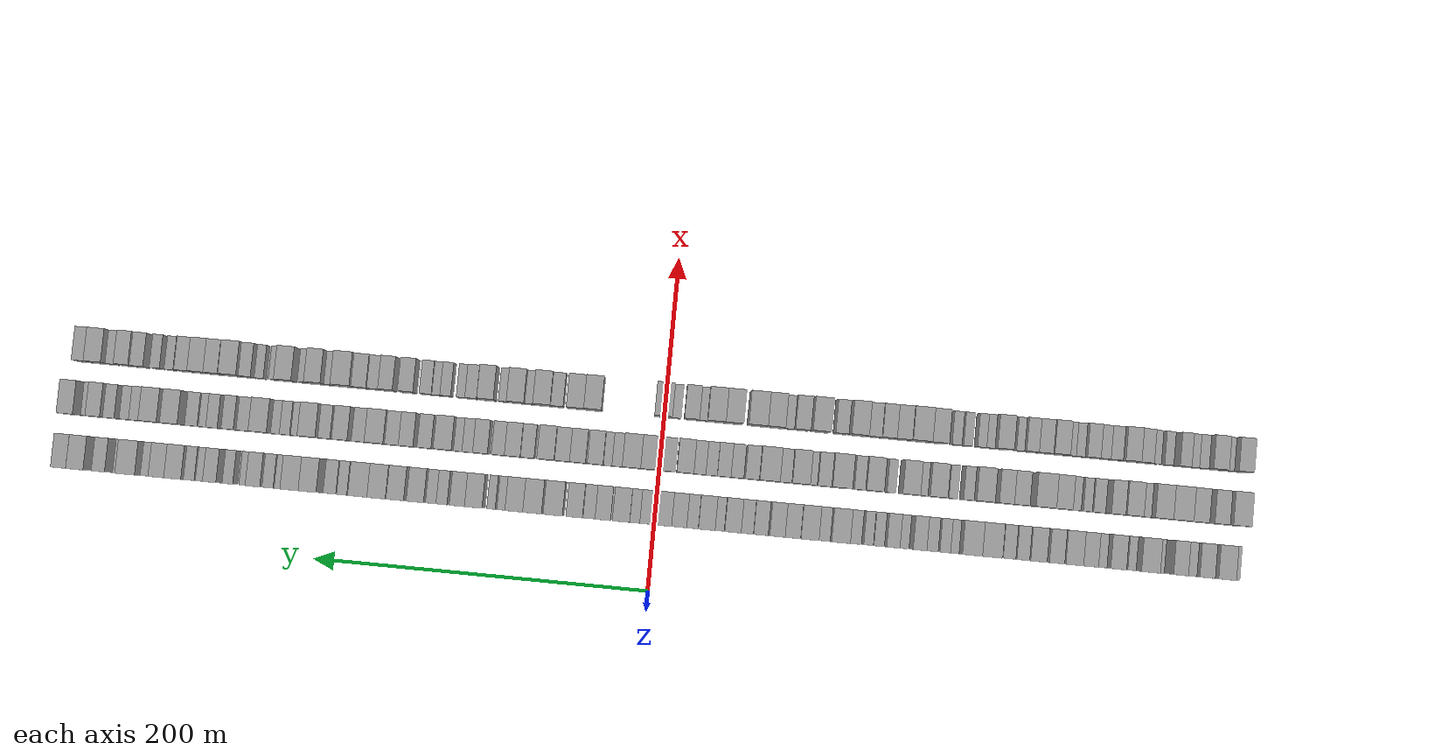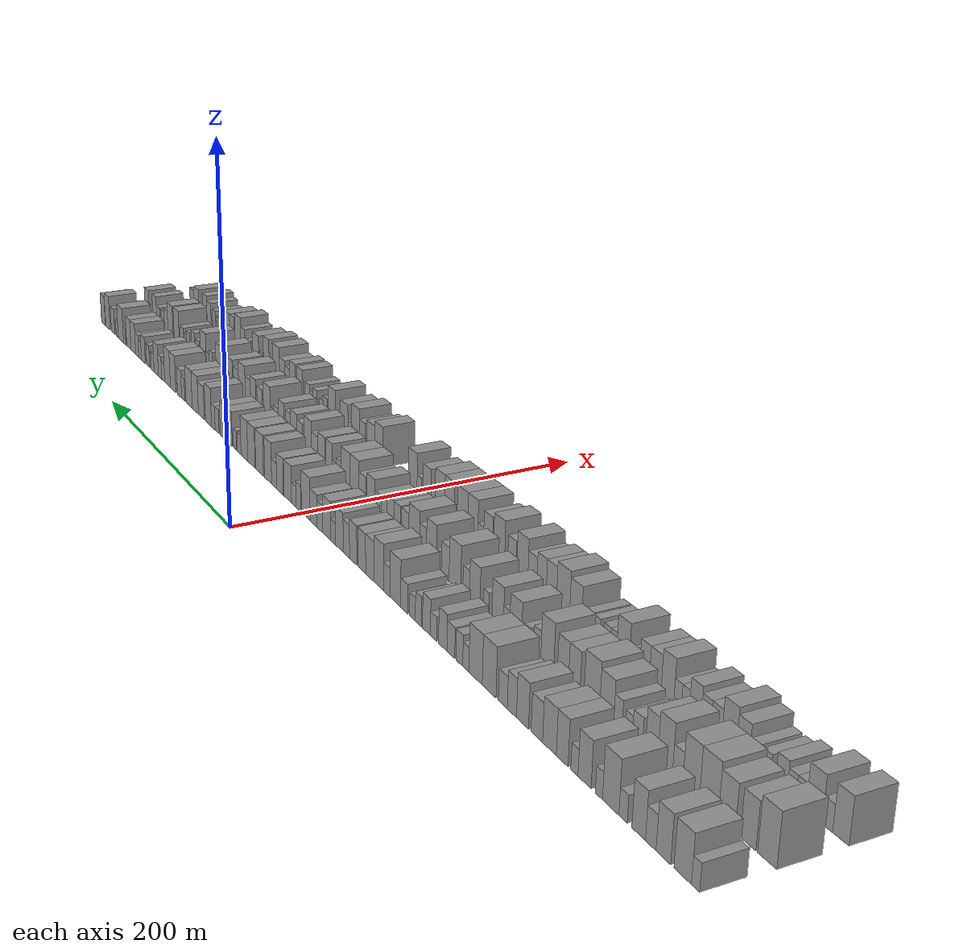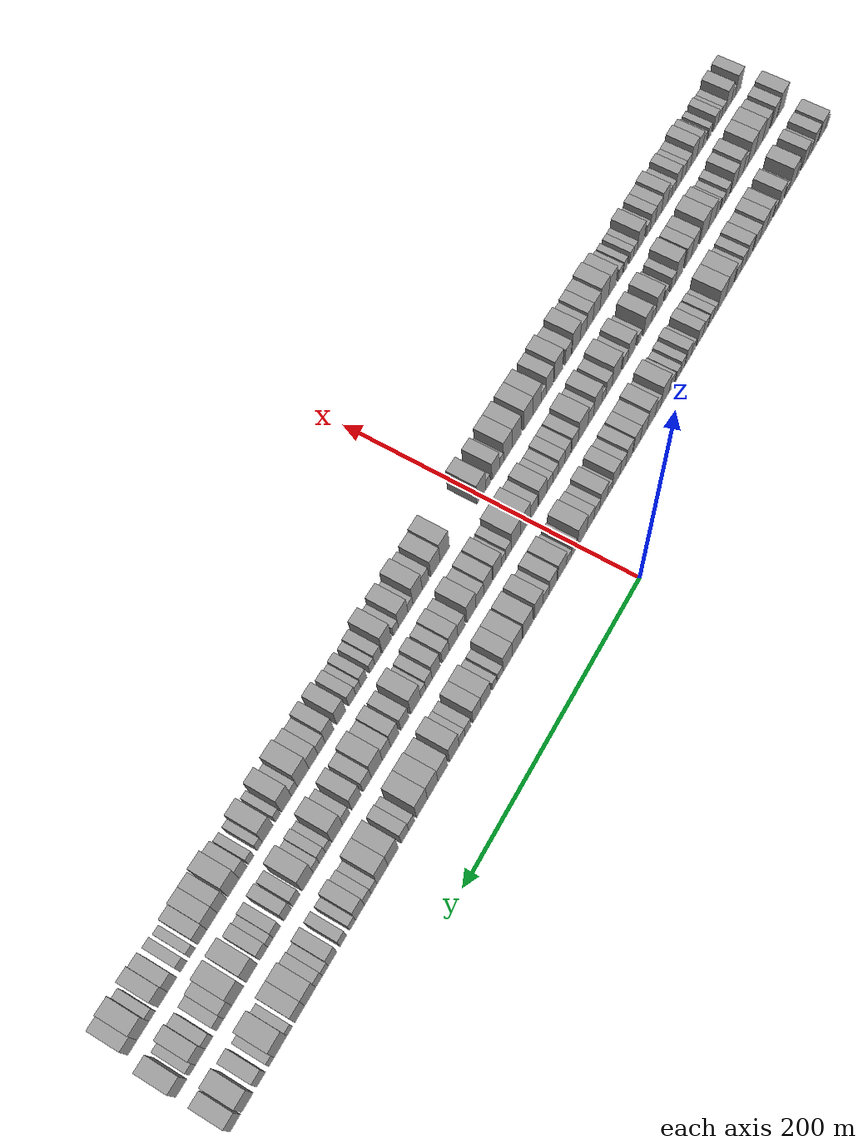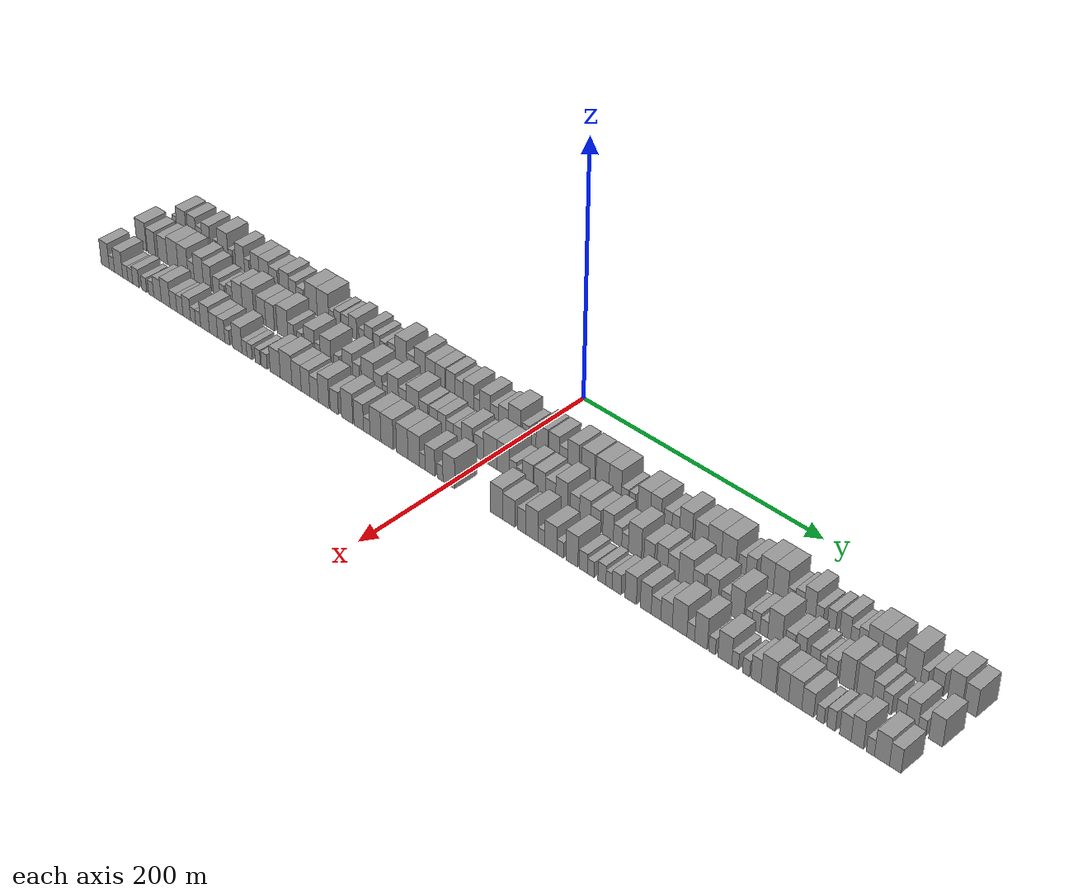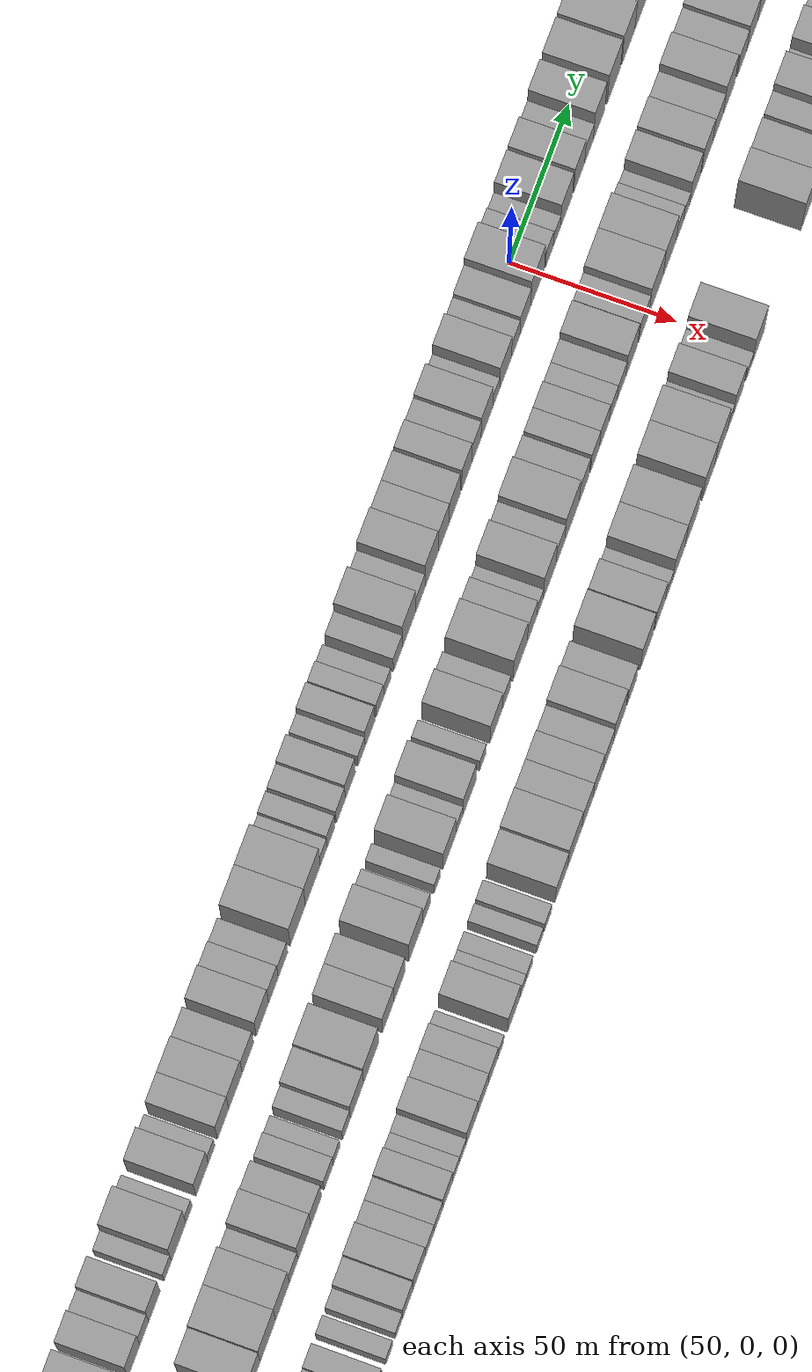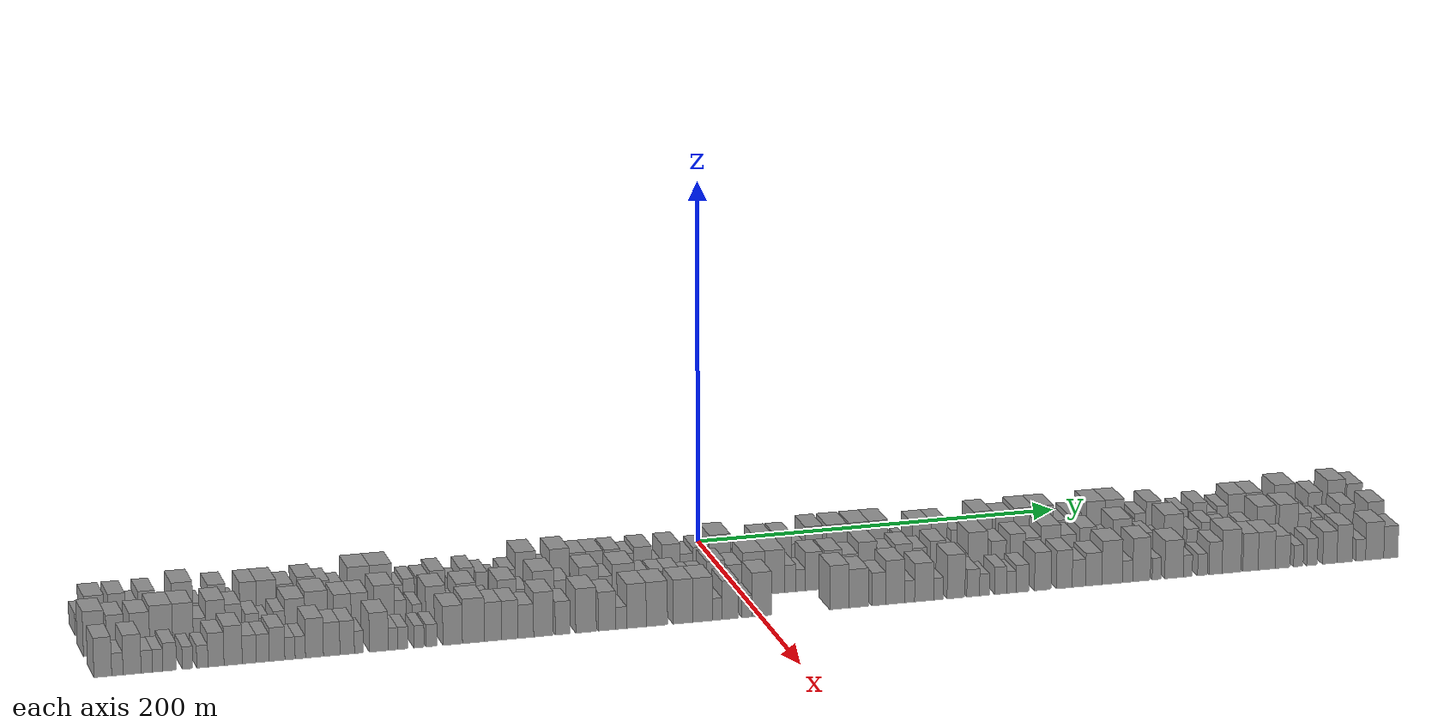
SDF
<sdf version="1.6">
 <world name="default">
  <scene>
   <sky><clouds><speed>12</speed></clouds></sky>
   <ambient>0.4 0.4 0.4 1</ambient>
   <background>0.7 0.7 0.7 1</background>
   <shadows>1</shadows>
  </scene>
  <gravity>0 0 -9.8066</gravity>
  <magnetic_field>6e-06 2.3e-05 -4.2e-05</magnetic_field>
  <physics default="0" name="default_physics" type="ode">
   <ode>
    <solver>
     <type>quick</type>
     <iters>10</iters>
     <sor>1.0</sor>
     <use_dynamic_moi_rescaling>0</use_dynamic_moi_rescaling>
    </solver>
    <constraints>
     <cfm>0</cfm>
     <erp>0.2</erp>
     <contact_max_correcting_vel>100</contact_max_correcting_vel>
     <contact_surface_layer>0.001</contact_surface_layer>
    </constraints>
   </ode>
   <max_step_size>0.004</max_step_size>
   <real_time_factor>1</real_time_factor>
   <real_time_update_rate>250</real_time_update_rate>
  </physics>
  <light name="sun" type="directional">
   <pose>0 0 10 0 0 0</pose>
   <diffuse>0.8 0.8 0.8 1</diffuse>
   <specular>0.2 0.2 0.2 1</specular>
   <attenuation>
    <range>1000</range>
    <constant>0.9</constant>
    <linear>0.01</linear>
    <quadratic>0.001</quadratic>
   </attenuation>
   <direction>-0.5 0.1 -0.9</direction>
  </light>
  <model name="building_1">
   <static>1</static>
   <pose>50.0000 -344.5965 0 0.000000 0.000000 0.000000</pose>
   <link name="link">
    <pose>0 0 6.00 0 0 0</pose>
    <collision name="collision"><geometry><box><size>20.0000 4.8070 12.0000</size></box></geometry></collision>
    <visual name="visual">
     <cast_shadows>0</cast_shadows>
     <geometry><box><size>20.0000 4.8070 12.0000</size></box></geometry>
     <material>
      <script>
       <uri>model://grey_wall/materials/scripts</uri>
       <uri>model://grey_wall/materials/textures</uri>
       <name>vrc/grey_wall</name>
      </script>
     </material>
    </visual>
   </link>
  </model>
  <model name="building_2">
   <static>1</static>
   <pose>50.0000 -336.9802 0 0.000000 0.000000 0.000000</pose>
   <link name="link">
    <pose>0 0 10.50 0 0 0</pose>
    <collision name="collision"><geometry><box><size>20.0000 10.4256 21.0000</size></box></geometry></collision>
    <visual name="visual">
     <cast_shadows>0</cast_shadows>
     <geometry><box><size>20.0000 10.4256 21.0000</size></box></geometry>
     <material>
      <script>
       <uri>model://grey_wall/materials/scripts</uri>
       <uri>model://grey_wall/materials/textures</uri>
       <name>vrc/grey_wall</name>
      </script>
     </material>
    </visual>
   </link>
  </model>
  <model name="building_3">
   <static>1</static>
   <pose>50.0000 -325.2521 0 0.000000 0.000000 0.000000</pose>
   <link name="link">
    <pose>0 0 10.50 0 0 0</pose>
    <collision name="collision"><geometry><box><size>20.0000 9.0307 21.0000</size></box></geometry></collision>
    <visual name="visual">
     <cast_shadows>0</cast_shadows>
     <geometry><box><size>20.0000 9.0307 21.0000</size></box></geometry>
     <material>
      <script>
       <uri>model://grey_wall/materials/scripts</uri>
       <uri>model://grey_wall/materials/textures</uri>
       <name>vrc/grey_wall</name>
      </script>
     </material>
    </visual>
   </link>
  </model>
  <model name="building_4">
   <static>1</static>
   <pose>50.0000 -317.3914 0 0.000000 0.000000 0.000000</pose>
   <link name="link">
    <pose>0 0 7.50 0 0 0</pose>
    <collision name="collision"><geometry><box><size>20.0000 6.6907 15.0000</size></box></geometry></collision>
    <visual name="visual">
     <cast_shadows>0</cast_shadows>
     <geometry><box><size>20.0000 6.6907 15.0000</size></box></geometry>
     <material>
      <script>
       <uri>model://grey_wall/materials/scripts</uri>
       <uri>model://grey_wall/materials/textures</uri>
       <name>vrc/grey_wall</name>
      </script>
     </material>
    </visual>
   </link>
  </model>
  <model name="building_5">
   <static>1</static>
   <pose>50.0000 -309.6811 0 0.000000 0.000000 0.000000</pose>
   <link name="link">
    <pose>0 0 10.50 0 0 0</pose>
    <collision name="collision"><geometry><box><size>20.0000 8.7298 21.0000</size></box></geometry></collision>
    <visual name="visual">
     <cast_shadows>0</cast_shadows>
     <geometry><box><size>20.0000 8.7298 21.0000</size></box></geometry>
     <material>
      <script>
       <uri>model://grey_wall/materials/scripts</uri>
       <uri>model://grey_wall/materials/textures</uri>
       <name>vrc/grey_wall</name>
      </script>
     </material>
    </visual>
   </link>
  </model>
  <model name="building_6">
   <static>1</static>
   <pose>50.0000 -299.5352 0 0.000000 0.000000 0.000000</pose>
   <link name="link">
    <pose>0 0 6.00 0 0 0</pose>
    <collision name="collision"><geometry><box><size>20.0000 5.5620 12.0000</size></box></geometry></collision>
    <visual name="visual">
     <cast_shadows>0</cast_shadows>
     <geometry><box><size>20.0000 5.5620 12.0000</size></box></geometry>
     <material>
      <script>
       <uri>model://grey_wall/materials/scripts</uri>
       <uri>model://grey_wall/materials/textures</uri>
       <name>vrc/grey_wall</name>
      </script>
     </material>
    </visual>
   </link>
  </model>
  <model name="building_7">
   <static>1</static>
   <pose>50.0000 -291.2199 0 0.000000 0.000000 0.000000</pose>
   <link name="link">
    <pose>0 0 12.00 0 0 0</pose>
    <collision name="collision"><geometry><box><size>20.0000 11.0687 24.0000</size></box></geometry></collision>
    <visual name="visual">
     <cast_shadows>0</cast_shadows>
     <geometry><box><size>20.0000 11.0687 24.0000</size></box></geometry>
     <material>
      <script>
       <uri>model://grey_wall/materials/scripts</uri>
       <uri>model://grey_wall/materials/textures</uri>
       <name>vrc/grey_wall</name>
      </script>
     </material>
    </visual>
   </link>
  </model>
  <model name="building_8">
   <static>1</static>
   <pose>50.0000 -283.2138 0 0.000000 0.000000 0.000000</pose>
   <link name="link">
    <pose>0 0 6.00 0 0 0</pose>
    <collision name="collision"><geometry><box><size>20.0000 4.9435 12.0000</size></box></geometry></collision>
    <visual name="visual">
     <cast_shadows>0</cast_shadows>
     <geometry><box><size>20.0000 4.9435 12.0000</size></box></geometry>
     <material>
      <script>
       <uri>model://grey_wall/materials/scripts</uri>
       <uri>model://grey_wall/materials/textures</uri>
       <name>vrc/grey_wall</name>
      </script>
     </material>
    </visual>
   </link>
  </model>
  <model name="building_9">
   <static>1</static>
   <pose>50.0000 -273.0751 0 0.000000 0.000000 0.000000</pose>
   <link name="link">
    <pose>0 0 10.50 0 0 0</pose>
    <collision name="collision"><geometry><box><size>20.0000 9.3339 21.0000</size></box></geometry></collision>
    <visual name="visual">
     <cast_shadows>0</cast_shadows>
     <geometry><box><size>20.0000 9.3339 21.0000</size></box></geometry>
     <material>
      <script>
       <uri>model://grey_wall/materials/scripts</uri>
       <uri>model://grey_wall/materials/textures</uri>
       <name>vrc/grey_wall</name>
      </script>
     </material>
    </visual>
   </link>
  </model>
  <model name="building_10">
   <static>1</static>
   <pose>50.0000 -265.8114 0 0.000000 0.000000 0.000000</pose>
   <link name="link">
    <pose>0 0 6.00 0 0 0</pose>
    <collision name="collision"><geometry><box><size>20.0000 5.1935 12.0000</size></box></geometry></collision>
    <visual name="visual">
     <cast_shadows>0</cast_shadows>
     <geometry><box><size>20.0000 5.1935 12.0000</size></box></geometry>
     <material>
      <script>
       <uri>model://grey_wall/materials/scripts</uri>
       <uri>model://grey_wall/materials/textures</uri>
       <name>vrc/grey_wall</name>
      </script>
     </material>
    </visual>
   </link>
  </model>
  <model name="building_11">
   <static>1</static>
   <pose>50.0000 -256.8526 0 0.000000 0.000000 0.000000</pose>
   <link name="link">
    <pose>0 0 10.50 0 0 0</pose>
    <collision name="collision"><geometry><box><size>20.0000 8.7240 21.0000</size></box></geometry></collision>
    <visual name="visual">
     <cast_shadows>0</cast_shadows>
     <geometry><box><size>20.0000 8.7240 21.0000</size></box></geometry>
     <material>
      <script>
       <uri>model://grey_wall/materials/scripts</uri>
       <uri>model://grey_wall/materials/textures</uri>
       <name>vrc/grey_wall</name>
      </script>
     </material>
    </visual>
   </link>
  </model>
  <model name="building_12">
   <static>1</static>
   <pose>50.0000 -247.2860 0 0.000000 0.000000 0.000000</pose>
   <link name="link">
    <pose>0 0 10.50 0 0 0</pose>
    <collision name="collision"><geometry><box><size>20.0000 10.4093 21.0000</size></box></geometry></collision>
    <visual name="visual">
     <cast_shadows>0</cast_shadows>
     <geometry><box><size>20.0000 10.4093 21.0000</size></box></geometry>
     <material>
      <script>
       <uri>model://grey_wall/materials/scripts</uri>
       <uri>model://grey_wall/materials/textures</uri>
       <name>vrc/grey_wall</name>
      </script>
     </material>
    </visual>
   </link>
  </model>
  <model name="building_13">
   <static>1</static>
   <pose>50.0000 -237.5903 0 0.000000 0.000000 0.000000</pose>
   <link name="link">
    <pose>0 0 9.00 0 0 0</pose>
    <collision name="collision"><geometry><box><size>20.0000 8.9820 18.0000</size></box></geometry></collision>
    <visual name="visual">
     <cast_shadows>0</cast_shadows>
     <geometry><box><size>20.0000 8.9820 18.0000</size></box></geometry>
     <material>
      <script>
       <uri>model://grey_wall/materials/scripts</uri>
       <uri>model://grey_wall/materials/textures</uri>
       <name>vrc/grey_wall</name>
      </script>
     </material>
    </visual>
   </link>
  </model>
  <model name="building_14">
   <static>1</static>
   <pose>50.0000 -226.2633 0 0.000000 0.000000 0.000000</pose>
   <link name="link">
    <pose>0 0 10.50 0 0 0</pose>
    <collision name="collision"><geometry><box><size>20.0000 9.6720 21.0000</size></box></geometry></collision>
    <visual name="visual">
     <cast_shadows>0</cast_shadows>
     <geometry><box><size>20.0000 9.6720 21.0000</size></box></geometry>
     <material>
      <script>
       <uri>model://grey_wall/materials/scripts</uri>
       <uri>model://grey_wall/materials/textures</uri>
       <name>vrc/grey_wall</name>
      </script>
     </material>
    </visual>
   </link>
  </model>
  <model name="building_15">
   <static>1</static>
   <pose>50.0000 -217.6535 0 0.000000 0.000000 0.000000</pose>
   <link name="link">
    <pose>0 0 9.00 0 0 0</pose>
    <collision name="collision"><geometry><box><size>20.0000 7.5478 18.0000</size></box></geometry></collision>
    <visual name="visual">
     <cast_shadows>0</cast_shadows>
     <geometry><box><size>20.0000 7.5478 18.0000</size></box></geometry>
     <material>
      <script>
       <uri>model://grey_wall/materials/scripts</uri>
       <uri>model://grey_wall/materials/textures</uri>
       <name>vrc/grey_wall</name>
      </script>
     </material>
    </visual>
   </link>
  </model>
  <model name="building_16">
   <static>1</static>
   <pose>50.0000 -210.1589 0 0.000000 0.000000 0.000000</pose>
   <link name="link">
    <pose>0 0 7.50 0 0 0</pose>
    <collision name="collision"><geometry><box><size>20.0000 7.4415 15.0000</size></box></geometry></collision>
    <visual name="visual">
     <cast_shadows>0</cast_shadows>
     <geometry><box><size>20.0000 7.4415 15.0000</size></box></geometry>
     <material>
      <script>
       <uri>model://grey_wall/materials/scripts</uri>
       <uri>model://grey_wall/materials/textures</uri>
       <name>vrc/grey_wall</name>
      </script>
     </material>
    </visual>
   </link>
  </model>
  <model name="building_17">
   <static>1</static>
   <pose>50.0000 -198.5323 0 0.000000 0.000000 0.000000</pose>
   <link name="link">
    <pose>0 0 12.00 0 0 0</pose>
    <collision name="collision"><geometry><box><size>20.0000 11.8116 24.0000</size></box></geometry></collision>
    <visual name="visual">
     <cast_shadows>0</cast_shadows>
     <geometry><box><size>20.0000 11.8116 24.0000</size></box></geometry>
     <material>
      <script>
       <uri>model://grey_wall/materials/scripts</uri>
       <uri>model://grey_wall/materials/textures</uri>
       <name>vrc/grey_wall</name>
      </script>
     </material>
    </visual>
   </link>
  </model>
  <model name="building_18">
   <static>1</static>
   <pose>50.0000 -186.7275 0 0.000000 0.000000 0.000000</pose>
   <link name="link">
    <pose>0 0 12.00 0 0 0</pose>
    <collision name="collision"><geometry><box><size>20.0000 11.7980 24.0000</size></box></geometry></collision>
    <visual name="visual">
     <cast_shadows>0</cast_shadows>
     <geometry><box><size>20.0000 11.7980 24.0000</size></box></geometry>
     <material>
      <script>
       <uri>model://grey_wall/materials/scripts</uri>
       <uri>model://grey_wall/materials/textures</uri>
       <name>vrc/grey_wall</name>
      </script>
     </material>
    </visual>
   </link>
  </model>
  <model name="building_19">
   <static>1</static>
   <pose>50.0000 -178.0555 0 0.000000 0.000000 0.000000</pose>
   <link name="link">
    <pose>0 0 6.00 0 0 0</pose>
    <collision name="collision"><geometry><box><size>20.0000 5.5461 12.0000</size></box></geometry></collision>
    <visual name="visual">
     <cast_shadows>0</cast_shadows>
     <geometry><box><size>20.0000 5.5461 12.0000</size></box></geometry>
     <material>
      <script>
       <uri>model://grey_wall/materials/scripts</uri>
       <uri>model://grey_wall/materials/textures</uri>
       <name>vrc/grey_wall</name>
      </script>
     </material>
    </visual>
   </link>
  </model>
  <model name="building_20">
   <static>1</static>
   <pose>50.0000 -172.1351 0 0.000000 0.000000 0.000000</pose>
   <link name="link">
    <pose>0 0 7.50 0 0 0</pose>
    <collision name="collision"><geometry><box><size>20.0000 6.2947 15.0000</size></box></geometry></collision>
    <visual name="visual">
     <cast_shadows>0</cast_shadows>
     <geometry><box><size>20.0000 6.2947 15.0000</size></box></geometry>
     <material>
      <script>
       <uri>model://grey_wall/materials/scripts</uri>
       <uri>model://grey_wall/materials/textures</uri>
       <name>vrc/grey_wall</name>
      </script>
     </material>
    </visual>
   </link>
  </model>
  <model name="building_21">
   <static>1</static>
   <pose>50.0000 -164.4153 0 0.000000 0.000000 0.000000</pose>
   <link name="link">
    <pose>0 0 7.50 0 0 0</pose>
    <collision name="collision"><geometry><box><size>20.0000 7.1448 15.0000</size></box></geometry></collision>
    <visual name="visual">
     <cast_shadows>0</cast_shadows>
     <geometry><box><size>20.0000 7.1448 15.0000</size></box></geometry>
     <material>
      <script>
       <uri>model://grey_wall/materials/scripts</uri>
       <uri>model://grey_wall/materials/textures</uri>
       <name>vrc/grey_wall</name>
      </script>
     </material>
    </visual>
   </link>
  </model>
  <model name="building_22">
   <static>1</static>
   <pose>50.0000 -156.8310 0 0.000000 0.000000 0.000000</pose>
   <link name="link">
    <pose>0 0 9.00 0 0 0</pose>
    <collision name="collision"><geometry><box><size>20.0000 8.0239 18.0000</size></box></geometry></collision>
    <visual name="visual">
     <cast_shadows>0</cast_shadows>
     <geometry><box><size>20.0000 8.0239 18.0000</size></box></geometry>
     <material>
      <script>
       <uri>model://grey_wall/materials/scripts</uri>
       <uri>model://grey_wall/materials/textures</uri>
       <name>vrc/grey_wall</name>
      </script>
     </material>
    </visual>
   </link>
  </model>
  <model name="building_23">
   <static>1</static>
   <pose>50.0000 -147.9092 0 0.000000 0.000000 0.000000</pose>
   <link name="link">
    <pose>0 0 6.00 0 0 0</pose>
    <collision name="collision"><geometry><box><size>20.0000 5.8197 12.0000</size></box></geometry></collision>
    <visual name="visual">
     <cast_shadows>0</cast_shadows>
     <geometry><box><size>20.0000 5.8197 12.0000</size></box></geometry>
     <material>
      <script>
       <uri>model://grey_wall/materials/scripts</uri>
       <uri>model://grey_wall/materials/textures</uri>
       <name>vrc/grey_wall</name>
      </script>
     </material>
    </visual>
   </link>
  </model>
  <model name="building_24">
   <static>1</static>
   <pose>50.0000 -141.1100 0 0.000000 0.000000 0.000000</pose>
   <link name="link">
    <pose>0 0 9.00 0 0 0</pose>
    <collision name="collision"><geometry><box><size>20.0000 7.7786 18.0000</size></box></geometry></collision>
    <visual name="visual">
     <cast_shadows>0</cast_shadows>
     <geometry><box><size>20.0000 7.7786 18.0000</size></box></geometry>
     <material>
      <script>
       <uri>model://grey_wall/materials/scripts</uri>
       <uri>model://grey_wall/materials/textures</uri>
       <name>vrc/grey_wall</name>
      </script>
     </material>
    </visual>
   </link>
  </model>
  <model name="building_25">
   <static>1</static>
   <pose>50.0000 -133.1322 0 0.000000 0.000000 0.000000</pose>
   <link name="link">
    <pose>0 0 7.50 0 0 0</pose>
    <collision name="collision"><geometry><box><size>20.0000 6.1768 15.0000</size></box></geometry></collision>
    <visual name="visual">
     <cast_shadows>0</cast_shadows>
     <geometry><box><size>20.0000 6.1768 15.0000</size></box></geometry>
     <material>
      <script>
       <uri>model://grey_wall/materials/scripts</uri>
       <uri>model://grey_wall/materials/textures</uri>
       <name>vrc/grey_wall</name>
      </script>
     </material>
    </visual>
   </link>
  </model>
  <model name="building_26">
   <static>1</static>
   <pose>50.0000 -127.1928 0 0.000000 0.000000 0.000000</pose>
   <link name="link">
    <pose>0 0 6.00 0 0 0</pose>
    <collision name="collision"><geometry><box><size>20.0000 5.7021 12.0000</size></box></geometry></collision>
    <visual name="visual">
     <cast_shadows>0</cast_shadows>
     <geometry><box><size>20.0000 5.7021 12.0000</size></box></geometry>
     <material>
      <script>
       <uri>model://grey_wall/materials/scripts</uri>
       <uri>model://grey_wall/materials/textures</uri>
       <name>vrc/grey_wall</name>
      </script>
     </material>
    </visual>
   </link>
  </model>
  <model name="building_27">
   <static>1</static>
   <pose>50.0000 -118.7382 0 0.000000 0.000000 0.000000</pose>
   <link name="link">
    <pose>0 0 7.50 0 0 0</pose>
    <collision name="collision"><geometry><box><size>20.0000 7.2071 15.0000</size></box></geometry></collision>
    <visual name="visual">
     <cast_shadows>0</cast_shadows>
     <geometry><box><size>20.0000 7.2071 15.0000</size></box></geometry>
     <material>
      <script>
       <uri>model://grey_wall/materials/scripts</uri>
       <uri>model://grey_wall/materials/textures</uri>
       <name>vrc/grey_wall</name>
      </script>
     </material>
    </visual>
   </link>
  </model>
  <model name="building_28">
   <static>1</static>
   <pose>50.0000 -109.6479 0 0.000000 0.000000 0.000000</pose>
   <link name="link">
    <pose>0 0 12.00 0 0 0</pose>
    <collision name="collision"><geometry><box><size>20.0000 10.9736 24.0000</size></box></geometry></collision>
    <visual name="visual">
     <cast_shadows>0</cast_shadows>
     <geometry><box><size>20.0000 10.9736 24.0000</size></box></geometry>
     <material>
      <script>
       <uri>model://grey_wall/materials/scripts</uri>
       <uri>model://grey_wall/materials/textures</uri>
       <name>vrc/grey_wall</name>
      </script>
     </material>
    </visual>
   </link>
  </model>
  <model name="building_29">
   <static>1</static>
   <pose>50.0000 -100.4507 0 0.000000 0.000000 0.000000</pose>
   <link name="link">
    <pose>0 0 7.50 0 0 0</pose>
    <collision name="collision"><geometry><box><size>20.0000 7.4209 15.0000</size></box></geometry></collision>
    <visual name="visual">
     <cast_shadows>0</cast_shadows>
     <geometry><box><size>20.0000 7.4209 15.0000</size></box></geometry>
     <material>
      <script>
       <uri>model://grey_wall/materials/scripts</uri>
       <uri>model://grey_wall/materials/textures</uri>
       <name>vrc/grey_wall</name>
      </script>
     </material>
    </visual>
   </link>
  </model>
  <model name="building_30">
   <static>1</static>
   <pose>50.0000 -91.4822 0 0.000000 0.000000 0.000000</pose>
   <link name="link">
    <pose>0 0 12.00 0 0 0</pose>
    <collision name="collision"><geometry><box><size>20.0000 10.5161 24.0000</size></box></geometry></collision>
    <visual name="visual">
     <cast_shadows>0</cast_shadows>
     <geometry><box><size>20.0000 10.5161 24.0000</size></box></geometry>
     <material>
      <script>
       <uri>model://grey_wall/materials/scripts</uri>
       <uri>model://grey_wall/materials/textures</uri>
       <name>vrc/grey_wall</name>
      </script>
     </material>
    </visual>
   </link>
  </model>
  <model name="building_31">
   <static>1</static>
   <pose>50.0000 -81.6602 0 0.000000 0.000000 0.000000</pose>
   <link name="link">
    <pose>0 0 10.50 0 0 0</pose>
    <collision name="collision"><geometry><box><size>20.0000 9.1278 21.0000</size></box></geometry></collision>
    <visual name="visual">
     <cast_shadows>0</cast_shadows>
     <geometry><box><size>20.0000 9.1278 21.0000</size></box></geometry>
     <material>
      <script>
       <uri>model://grey_wall/materials/scripts</uri>
       <uri>model://grey_wall/materials/textures</uri>
       <name>vrc/grey_wall</name>
      </script>
     </material>
    </visual>
   </link>
  </model>
  <model name="building_32">
   <static>1</static>
   <pose>50.0000 -72.5824 0 0.000000 0.000000 0.000000</pose>
   <link name="link">
    <pose>0 0 10.50 0 0 0</pose>
    <collision name="collision"><geometry><box><size>20.0000 9.0279 21.0000</size></box></geometry></collision>
    <visual name="visual">
     <cast_shadows>0</cast_shadows>
     <geometry><box><size>20.0000 9.0279 21.0000</size></box></geometry>
     <material>
      <script>
       <uri>model://grey_wall/materials/scripts</uri>
       <uri>model://grey_wall/materials/textures</uri>
       <name>vrc/grey_wall</name>
      </script>
     </material>
    </visual>
   </link>
  </model>
  <model name="building_33">
   <static>1</static>
   <pose>50.0000 -62.8511 0 0.000000 0.000000 0.000000</pose>
   <link name="link">
    <pose>0 0 10.50 0 0 0</pose>
    <collision name="collision"><geometry><box><size>20.0000 8.4345 21.0000</size></box></geometry></collision>
    <visual name="visual">
     <cast_shadows>0</cast_shadows>
     <geometry><box><size>20.0000 8.4345 21.0000</size></box></geometry>
     <material>
      <script>
       <uri>model://grey_wall/materials/scripts</uri>
       <uri>model://grey_wall/materials/textures</uri>
       <name>vrc/grey_wall</name>
      </script>
     </material>
    </visual>
   </link>
  </model>
  <model name="building_34">
   <static>1</static>
   <pose>50.0000 -54.9011 0 0.000000 0.000000 0.000000</pose>
   <link name="link">
    <pose>0 0 9.00 0 0 0</pose>
    <collision name="collision"><geometry><box><size>20.0000 7.4656 18.0000</size></box></geometry></collision>
    <visual name="visual">
     <cast_shadows>0</cast_shadows>
     <geometry><box><size>20.0000 7.4656 18.0000</size></box></geometry>
     <material>
      <script>
       <uri>model://grey_wall/materials/scripts</uri>
       <uri>model://grey_wall/materials/textures</uri>
       <name>vrc/grey_wall</name>
      </script>
     </material>
    </visual>
   </link>
  </model>
  <model name="building_35">
   <static>1</static>
   <pose>50.0000 -46.3791 0 0.000000 0.000000 0.000000</pose>
   <link name="link">
    <pose>0 0 10.50 0 0 0</pose>
    <collision name="collision"><geometry><box><size>20.0000 9.5783 21.0000</size></box></geometry></collision>
    <visual name="visual">
     <cast_shadows>0</cast_shadows>
     <geometry><box><size>20.0000 9.5783 21.0000</size></box></geometry>
     <material>
      <script>
       <uri>model://grey_wall/materials/scripts</uri>
       <uri>model://grey_wall/materials/textures</uri>
       <name>vrc/grey_wall</name>
      </script>
     </material>
    </visual>
   </link>
  </model>
  <model name="building_36">
   <static>1</static>
   <pose>50.0000 -38.7108 0 0.000000 0.000000 0.000000</pose>
   <link name="link">
    <pose>0 0 6.00 0 0 0</pose>
    <collision name="collision"><geometry><box><size>20.0000 5.7583 12.0000</size></box></geometry></collision>
    <visual name="visual">
     <cast_shadows>0</cast_shadows>
     <geometry><box><size>20.0000 5.7583 12.0000</size></box></geometry>
     <material>
      <script>
       <uri>model://grey_wall/materials/scripts</uri>
       <uri>model://grey_wall/materials/textures</uri>
       <name>vrc/grey_wall</name>
      </script>
     </material>
    </visual>
   </link>
  </model>
  <model name="building_37">
   <static>1</static>
   <pose>50.0000 -30.9705 0 0.000000 0.000000 0.000000</pose>
   <link name="link">
    <pose>0 0 10.50 0 0 0</pose>
    <collision name="collision"><geometry><box><size>20.0000 9.7223 21.0000</size></box></geometry></collision>
    <visual name="visual">
     <cast_shadows>0</cast_shadows>
     <geometry><box><size>20.0000 9.7223 21.0000</size></box></geometry>
     <material>
      <script>
       <uri>model://grey_wall/materials/scripts</uri>
       <uri>model://grey_wall/materials/textures</uri>
       <name>vrc/grey_wall</name>
      </script>
     </material>
    </visual>
   </link>
  </model>
  <model name="building_38">
   <static>1</static>
   <pose>50.0000 -22.6465 0 0.000000 0.000000 0.000000</pose>
   <link name="link">
    <pose>0 0 7.50 0 0 0</pose>
    <collision name="collision"><geometry><box><size>20.0000 6.9256 15.0000</size></box></geometry></collision>
    <visual name="visual">
     <cast_shadows>0</cast_shadows>
     <geometry><box><size>20.0000 6.9256 15.0000</size></box></geometry>
     <material>
      <script>
       <uri>model://grey_wall/materials/scripts</uri>
       <uri>model://grey_wall/materials/textures</uri>
       <name>vrc/grey_wall</name>
      </script>
     </material>
    </visual>
   </link>
  </model>
  <model name="building_39">
   <static>1</static>
   <pose>50.0000 -14.6906 0 0.000000 0.000000 0.000000</pose>
   <link name="link">
    <pose>0 0 9.00 0 0 0</pose>
    <collision name="collision"><geometry><box><size>20.0000 8.9863 18.0000</size></box></geometry></collision>
    <visual name="visual">
     <cast_shadows>0</cast_shadows>
     <geometry><box><size>20.0000 8.9863 18.0000</size></box></geometry>
     <material>
      <script>
       <uri>model://grey_wall/materials/scripts</uri>
       <uri>model://grey_wall/materials/textures</uri>
       <name>vrc/grey_wall</name>
      </script>
     </material>
    </visual>
   </link>
  </model>
  <model name="building_40">
   <static>1</static>
   <pose>50.0000 -4.5184 0 0.000000 0.000000 0.000000</pose>
   <link name="link">
    <pose>0 0 12.00 0 0 0</pose>
    <collision name="collision"><geometry><box><size>20.0000 11.3580 24.0000</size></box></geometry></collision>
    <visual name="visual">
     <cast_shadows>0</cast_shadows>
     <geometry><box><size>20.0000 11.3580 24.0000</size></box></geometry>
     <material>
      <script>
       <uri>model://grey_wall/materials/scripts</uri>
       <uri>model://grey_wall/materials/textures</uri>
       <name>vrc/grey_wall</name>
      </script>
     </material>
    </visual>
   </link>
  </model>
  <model name="building_41">
   <static>1</static>
   <pose>50.0000 5.3556 0 0.000000 0.000000 0.000000</pose>
   <link name="link">
    <pose>0 0 7.50 0 0 0</pose>
    <collision name="collision"><geometry><box><size>20.0000 6.3901 15.0000</size></box></geometry></collision>
    <visual name="visual">
     <cast_shadows>0</cast_shadows>
     <geometry><box><size>20.0000 6.3901 15.0000</size></box></geometry>
     <material>
      <script>
       <uri>model://grey_wall/materials/scripts</uri>
       <uri>model://grey_wall/materials/textures</uri>
       <name>vrc/grey_wall</name>
      </script>
     </material>
    </visual>
   </link>
  </model>
  <model name="building_42">
   <static>1</static>
   <pose>50.0000 11.5126 0 0.000000 0.000000 0.000000</pose>
   <link name="link">
    <pose>0 0 6.00 0 0 0</pose>
    <collision name="collision"><geometry><box><size>20.0000 5.9239 12.0000</size></box></geometry></collision>
    <visual name="visual">
     <cast_shadows>0</cast_shadows>
     <geometry><box><size>20.0000 5.9239 12.0000</size></box></geometry>
     <material>
      <script>
       <uri>model://grey_wall/materials/scripts</uri>
       <uri>model://grey_wall/materials/textures</uri>
       <name>vrc/grey_wall</name>
      </script>
     </material>
    </visual>
   </link>
  </model>
  <model name="building_43">
   <static>1</static>
   <pose>50.0000 19.5705 0 0.000000 0.000000 0.000000</pose>
   <link name="link">
    <pose>0 0 10.50 0 0 0</pose>
    <collision name="collision"><geometry><box><size>20.0000 10.1919 21.0000</size></box></geometry></collision>
    <visual name="visual">
     <cast_shadows>0</cast_shadows>
     <geometry><box><size>20.0000 10.1919 21.0000</size></box></geometry>
     <material>
      <script>
       <uri>model://grey_wall/materials/scripts</uri>
       <uri>model://grey_wall/materials/textures</uri>
       <name>vrc/grey_wall</name>
      </script>
     </material>
    </visual>
   </link>
  </model>
  <model name="building_44">
   <static>1</static>
   <pose>50.0000 30.2833 0 0.000000 0.000000 0.000000</pose>
   <link name="link">
    <pose>0 0 10.50 0 0 0</pose>
    <collision name="collision"><geometry><box><size>20.0000 9.2336 21.0000</size></box></geometry></collision>
    <visual name="visual">
     <cast_shadows>0</cast_shadows>
     <geometry><box><size>20.0000 9.2336 21.0000</size></box></geometry>
     <material>
      <script>
       <uri>model://grey_wall/materials/scripts</uri>
       <uri>model://grey_wall/materials/textures</uri>
       <name>vrc/grey_wall</name>
      </script>
     </material>
    </visual>
   </link>
  </model>
  <model name="building_45">
   <static>1</static>
   <pose>50.0000 38.5328 0 0.000000 0.000000 0.000000</pose>
   <link name="link">
    <pose>0 0 7.50 0 0 0</pose>
    <collision name="collision"><geometry><box><size>20.0000 7.2654 15.0000</size></box></geometry></collision>
    <visual name="visual">
     <cast_shadows>0</cast_shadows>
     <geometry><box><size>20.0000 7.2654 15.0000</size></box></geometry>
     <material>
      <script>
       <uri>model://grey_wall/materials/scripts</uri>
       <uri>model://grey_wall/materials/textures</uri>
       <name>vrc/grey_wall</name>
      </script>
     </material>
    </visual>
   </link>
  </model>
  <model name="building_46">
   <static>1</static>
   <pose>50.0000 47.0347 0 0.000000 0.000000 0.000000</pose>
   <link name="link">
    <pose>0 0 12.00 0 0 0</pose>
    <collision name="collision"><geometry><box><size>20.0000 9.7384 24.0000</size></box></geometry></collision>
    <visual name="visual">
     <cast_shadows>0</cast_shadows>
     <geometry><box><size>20.0000 9.7384 24.0000</size></box></geometry>
     <material>
      <script>
       <uri>model://grey_wall/materials/scripts</uri>
       <uri>model://grey_wall/materials/textures</uri>
       <name>vrc/grey_wall</name>
      </script>
     </material>
    </visual>
   </link>
  </model>
  <model name="building_47">
   <static>1</static>
   <pose>50.0000 59.5788 0 0.000000 0.000000 0.000000</pose>
   <link name="link">
    <pose>0 0 12.00 0 0 0</pose>
    <collision name="collision"><geometry><box><size>20.0000 11.3498 24.0000</size></box></geometry></collision>
    <visual name="visual">
     <cast_shadows>0</cast_shadows>
     <geometry><box><size>20.0000 11.3498 24.0000</size></box></geometry>
     <material>
      <script>
       <uri>model://grey_wall/materials/scripts</uri>
       <uri>model://grey_wall/materials/textures</uri>
       <name>vrc/grey_wall</name>
      </script>
     </material>
    </visual>
   </link>
  </model>
  <model name="building_48">
   <static>1</static>
   <pose>50.0000 71.7756 0 0.000000 0.000000 0.000000</pose>
   <link name="link">
    <pose>0 0 12.00 0 0 0</pose>
    <collision name="collision"><geometry><box><size>20.0000 11.0438 24.0000</size></box></geometry></collision>
    <visual name="visual">
     <cast_shadows>0</cast_shadows>
     <geometry><box><size>20.0000 11.0438 24.0000</size></box></geometry>
     <material>
      <script>
       <uri>model://grey_wall/materials/scripts</uri>
       <uri>model://grey_wall/materials/textures</uri>
       <name>vrc/grey_wall</name>
      </script>
     </material>
    </visual>
   </link>
  </model>
  <model name="building_49">
   <static>1</static>
   <pose>50.0000 82.5181 0 0.000000 0.000000 0.000000</pose>
   <link name="link">
    <pose>0 0 12.00 0 0 0</pose>
    <collision name="collision"><geometry><box><size>20.0000 10.4412 24.0000</size></box></geometry></collision>
    <visual name="visual">
     <cast_shadows>0</cast_shadows>
     <geometry><box><size>20.0000 10.4412 24.0000</size></box></geometry>
     <material>
      <script>
       <uri>model://grey_wall/materials/scripts</uri>
       <uri>model://grey_wall/materials/textures</uri>
       <name>vrc/grey_wall</name>
      </script>
     </material>
    </visual>
   </link>
  </model>
  <model name="building_50">
   <static>1</static>
   <pose>50.0000 90.5977 0 0.000000 0.000000 0.000000</pose>
   <link name="link">
    <pose>0 0 6.00 0 0 0</pose>
    <collision name="collision"><geometry><box><size>20.0000 5.7179 12.0000</size></box></geometry></collision>
    <visual name="visual">
     <cast_shadows>0</cast_shadows>
     <geometry><box><size>20.0000 5.7179 12.0000</size></box></geometry>
     <material>
      <script>
       <uri>model://grey_wall/materials/scripts</uri>
       <uri>model://grey_wall/materials/textures</uri>
       <name>vrc/grey_wall</name>
      </script>
     </material>
    </visual>
   </link>
  </model>
  <model name="building_51">
   <static>1</static>
   <pose>50.0000 96.9436 0 0.000000 0.000000 0.000000</pose>
   <link name="link">
    <pose>0 0 6.00 0 0 0</pose>
    <collision name="collision"><geometry><box><size>20.0000 4.9740 12.0000</size></box></geometry></collision>
    <visual name="visual">
     <cast_shadows>0</cast_shadows>
     <geometry><box><size>20.0000 4.9740 12.0000</size></box></geometry>
     <material>
      <script>
       <uri>model://grey_wall/materials/scripts</uri>
       <uri>model://grey_wall/materials/textures</uri>
       <name>vrc/grey_wall</name>
      </script>
     </material>
    </visual>
   </link>
  </model>
  <model name="building_52">
   <static>1</static>
   <pose>50.0000 106.6325 0 0.000000 0.000000 0.000000</pose>
   <link name="link">
    <pose>0 0 10.50 0 0 0</pose>
    <collision name="collision"><geometry><box><size>20.0000 10.4038 21.0000</size></box></geometry></collision>
    <visual name="visual">
     <cast_shadows>0</cast_shadows>
     <geometry><box><size>20.0000 10.4038 21.0000</size></box></geometry>
     <material>
      <script>
       <uri>model://grey_wall/materials/scripts</uri>
       <uri>model://grey_wall/materials/textures</uri>
       <name>vrc/grey_wall</name>
      </script>
     </material>
    </visual>
   </link>
  </model>
  <model name="building_53">
   <static>1</static>
   <pose>50.0000 116.3029 0 0.000000 0.000000 0.000000</pose>
   <link name="link">
    <pose>0 0 10.50 0 0 0</pose>
    <collision name="collision"><geometry><box><size>20.0000 8.9370 21.0000</size></box></geometry></collision>
    <visual name="visual">
     <cast_shadows>0</cast_shadows>
     <geometry><box><size>20.0000 8.9370 21.0000</size></box></geometry>
     <material>
      <script>
       <uri>model://grey_wall/materials/scripts</uri>
       <uri>model://grey_wall/materials/textures</uri>
       <name>vrc/grey_wall</name>
      </script>
     </material>
    </visual>
   </link>
  </model>
  <model name="building_54">
   <static>1</static>
   <pose>50.0000 126.0324 0 0.000000 0.000000 0.000000</pose>
   <link name="link">
    <pose>0 0 7.50 0 0 0</pose>
    <collision name="collision"><geometry><box><size>20.0000 6.5221 15.0000</size></box></geometry></collision>
    <visual name="visual">
     <cast_shadows>0</cast_shadows>
     <geometry><box><size>20.0000 6.5221 15.0000</size></box></geometry>
     <material>
      <script>
       <uri>model://grey_wall/materials/scripts</uri>
       <uri>model://grey_wall/materials/textures</uri>
       <name>vrc/grey_wall</name>
      </script>
     </material>
    </visual>
   </link>
  </model>
  <model name="building_55">
   <static>1</static>
   <pose>50.0000 132.4087 0 0.000000 0.000000 0.000000</pose>
   <link name="link">
    <pose>0 0 7.50 0 0 0</pose>
    <collision name="collision"><geometry><box><size>20.0000 6.2305 15.0000</size></box></geometry></collision>
    <visual name="visual">
     <cast_shadows>0</cast_shadows>
     <geometry><box><size>20.0000 6.2305 15.0000</size></box></geometry>
     <material>
      <script>
       <uri>model://grey_wall/materials/scripts</uri>
       <uri>model://grey_wall/materials/textures</uri>
       <name>vrc/grey_wall</name>
      </script>
     </material>
    </visual>
   </link>
  </model>
  <model name="building_56">
   <static>1</static>
   <pose>50.0000 140.6190 0 0.000000 0.000000 0.000000</pose>
   <link name="link">
    <pose>0 0 12.00 0 0 0</pose>
    <collision name="collision"><geometry><box><size>20.0000 10.1901 24.0000</size></box></geometry></collision>
    <visual name="visual">
     <cast_shadows>0</cast_shadows>
     <geometry><box><size>20.0000 10.1901 24.0000</size></box></geometry>
     <material>
      <script>
       <uri>model://grey_wall/materials/scripts</uri>
       <uri>model://grey_wall/materials/textures</uri>
       <name>vrc/grey_wall</name>
      </script>
     </material>
    </visual>
   </link>
  </model>
  <model name="building_57">
   <static>1</static>
   <pose>50.0000 152.8733 0 0.000000 0.000000 0.000000</pose>
   <link name="link">
    <pose>0 0 10.50 0 0 0</pose>
    <collision name="collision"><geometry><box><size>20.0000 10.3183 21.0000</size></box></geometry></collision>
    <visual name="visual">
     <cast_shadows>0</cast_shadows>
     <geometry><box><size>20.0000 10.3183 21.0000</size></box></geometry>
     <material>
      <script>
       <uri>model://grey_wall/materials/scripts</uri>
       <uri>model://grey_wall/materials/textures</uri>
       <name>vrc/grey_wall</name>
      </script>
     </material>
    </visual>
   </link>
  </model>
  <model name="building_58">
   <static>1</static>
   <pose>50.0000 163.4792 0 0.000000 0.000000 0.000000</pose>
   <link name="link">
    <pose>0 0 12.00 0 0 0</pose>
    <collision name="collision"><geometry><box><size>20.0000 10.8936 24.0000</size></box></geometry></collision>
    <visual name="visual">
     <cast_shadows>0</cast_shadows>
     <geometry><box><size>20.0000 10.8936 24.0000</size></box></geometry>
     <material>
      <script>
       <uri>model://grey_wall/materials/scripts</uri>
       <uri>model://grey_wall/materials/textures</uri>
       <name>vrc/grey_wall</name>
      </script>
     </material>
    </visual>
   </link>
  </model>
  <model name="building_59">
   <static>1</static>
   <pose>50.0000 174.5568 0 0.000000 0.000000 0.000000</pose>
   <link name="link">
    <pose>0 0 12.00 0 0 0</pose>
    <collision name="collision"><geometry><box><size>20.0000 11.2616 24.0000</size></box></geometry></collision>
    <visual name="visual">
     <cast_shadows>0</cast_shadows>
     <geometry><box><size>20.0000 11.2616 24.0000</size></box></geometry>
     <material>
      <script>
       <uri>model://grey_wall/materials/scripts</uri>
       <uri>model://grey_wall/materials/textures</uri>
       <name>vrc/grey_wall</name>
      </script>
     </material>
    </visual>
   </link>
  </model>
  <model name="building_60">
   <static>1</static>
   <pose>50.0000 185.1954 0 0.000000 0.000000 0.000000</pose>
   <link name="link">
    <pose>0 0 7.50 0 0 0</pose>
    <collision name="collision"><geometry><box><size>20.0000 6.0156 15.0000</size></box></geometry></collision>
    <visual name="visual">
     <cast_shadows>0</cast_shadows>
     <geometry><box><size>20.0000 6.0156 15.0000</size></box></geometry>
     <material>
      <script>
       <uri>model://grey_wall/materials/scripts</uri>
       <uri>model://grey_wall/materials/textures</uri>
       <name>vrc/grey_wall</name>
      </script>
     </material>
    </visual>
   </link>
  </model>
  <model name="building_61">
   <static>1</static>
   <pose>50.0000 191.9791 0 0.000000 0.000000 0.000000</pose>
   <link name="link">
    <pose>0 0 9.00 0 0 0</pose>
    <collision name="collision"><geometry><box><size>20.0000 7.5519 18.0000</size></box></geometry></collision>
    <visual name="visual">
     <cast_shadows>0</cast_shadows>
     <geometry><box><size>20.0000 7.5519 18.0000</size></box></geometry>
     <material>
      <script>
       <uri>model://grey_wall/materials/scripts</uri>
       <uri>model://grey_wall/materials/textures</uri>
       <name>vrc/grey_wall</name>
      </script>
     </material>
    </visual>
   </link>
  </model>
  <model name="building_62">
   <static>1</static>
   <pose>50.0000 204.0300 0 0.000000 0.000000 0.000000</pose>
   <link name="link">
    <pose>0 0 12.00 0 0 0</pose>
    <collision name="collision"><geometry><box><size>20.0000 10.5499 24.0000</size></box></geometry></collision>
    <visual name="visual">
     <cast_shadows>0</cast_shadows>
     <geometry><box><size>20.0000 10.5499 24.0000</size></box></geometry>
     <material>
      <script>
       <uri>model://grey_wall/materials/scripts</uri>
       <uri>model://grey_wall/materials/textures</uri>
       <name>vrc/grey_wall</name>
      </script>
     </material>
    </visual>
   </link>
  </model>
  <model name="building_63">
   <static>1</static>
   <pose>50.0000 214.6708 0 0.000000 0.000000 0.000000</pose>
   <link name="link">
    <pose>0 0 12.00 0 0 0</pose>
    <collision name="collision"><geometry><box><size>20.0000 10.7318 24.0000</size></box></geometry></collision>
    <visual name="visual">
     <cast_shadows>0</cast_shadows>
     <geometry><box><size>20.0000 10.7318 24.0000</size></box></geometry>
     <material>
      <script>
       <uri>model://grey_wall/materials/scripts</uri>
       <uri>model://grey_wall/materials/textures</uri>
       <name>vrc/grey_wall</name>
      </script>
     </material>
    </visual>
   </link>
  </model>
  <model name="building_64">
   <static>1</static>
   <pose>50.0000 222.9557 0 0.000000 0.000000 0.000000</pose>
   <link name="link">
    <pose>0 0 6.00 0 0 0</pose>
    <collision name="collision"><geometry><box><size>20.0000 5.8381 12.0000</size></box></geometry></collision>
    <visual name="visual">
     <cast_shadows>0</cast_shadows>
     <geometry><box><size>20.0000 5.8381 12.0000</size></box></geometry>
     <material>
      <script>
       <uri>model://grey_wall/materials/scripts</uri>
       <uri>model://grey_wall/materials/textures</uri>
       <name>vrc/grey_wall</name>
      </script>
     </material>
    </visual>
   </link>
  </model>
  <model name="building_65">
   <static>1</static>
   <pose>50.0000 229.1912 0 0.000000 0.000000 0.000000</pose>
   <link name="link">
    <pose>0 0 7.50 0 0 0</pose>
    <collision name="collision"><geometry><box><size>20.0000 6.6328 15.0000</size></box></geometry></collision>
    <visual name="visual">
     <cast_shadows>0</cast_shadows>
     <geometry><box><size>20.0000 6.6328 15.0000</size></box></geometry>
     <material>
      <script>
       <uri>model://grey_wall/materials/scripts</uri>
       <uri>model://grey_wall/materials/textures</uri>
       <name>vrc/grey_wall</name>
      </script>
     </material>
    </visual>
   </link>
  </model>
  <model name="building_66">
   <static>1</static>
   <pose>50.0000 236.8308 0 0.000000 0.000000 0.000000</pose>
   <link name="link">
    <pose>0 0 10.50 0 0 0</pose>
    <collision name="collision"><geometry><box><size>20.0000 8.6464 21.0000</size></box></geometry></collision>
    <visual name="visual">
     <cast_shadows>0</cast_shadows>
     <geometry><box><size>20.0000 8.6464 21.0000</size></box></geometry>
     <material>
      <script>
       <uri>model://grey_wall/materials/scripts</uri>
       <uri>model://grey_wall/materials/textures</uri>
       <name>vrc/grey_wall</name>
      </script>
     </material>
    </visual>
   </link>
  </model>
  <model name="building_67">
   <static>1</static>
   <pose>50.0000 244.0152 0 0.000000 0.000000 0.000000</pose>
   <link name="link">
    <pose>0 0 6.00 0 0 0</pose>
    <collision name="collision"><geometry><box><size>20.0000 5.7225 12.0000</size></box></geometry></collision>
    <visual name="visual">
     <cast_shadows>0</cast_shadows>
     <geometry><box><size>20.0000 5.7225 12.0000</size></box></geometry>
     <material>
      <script>
       <uri>model://grey_wall/materials/scripts</uri>
       <uri>model://grey_wall/materials/textures</uri>
       <name>vrc/grey_wall</name>
      </script>
     </material>
    </visual>
   </link>
  </model>
  <model name="building_68">
   <static>1</static>
   <pose>50.0000 253.0156 0 0.000000 0.000000 0.000000</pose>
   <link name="link">
    <pose>0 0 7.50 0 0 0</pose>
    <collision name="collision"><geometry><box><size>20.0000 6.2782 15.0000</size></box></geometry></collision>
    <visual name="visual">
     <cast_shadows>0</cast_shadows>
     <geometry><box><size>20.0000 6.2782 15.0000</size></box></geometry>
     <material>
      <script>
       <uri>model://grey_wall/materials/scripts</uri>
       <uri>model://grey_wall/materials/textures</uri>
       <name>vrc/grey_wall</name>
      </script>
     </material>
    </visual>
   </link>
  </model>
  <model name="building_69">
   <static>1</static>
   <pose>50.0000 263.1421 0 0.000000 0.000000 0.000000</pose>
   <link name="link">
    <pose>0 0 9.00 0 0 0</pose>
    <collision name="collision"><geometry><box><size>20.0000 7.9747 18.0000</size></box></geometry></collision>
    <visual name="visual">
     <cast_shadows>0</cast_shadows>
     <geometry><box><size>20.0000 7.9747 18.0000</size></box></geometry>
     <material>
      <script>
       <uri>model://grey_wall/materials/scripts</uri>
       <uri>model://grey_wall/materials/textures</uri>
       <name>vrc/grey_wall</name>
      </script>
     </material>
    </visual>
   </link>
  </model>
  <model name="building_70">
   <static>1</static>
   <pose>50.0000 269.9573 0 0.000000 0.000000 0.000000</pose>
   <link name="link">
    <pose>0 0 6.00 0 0 0</pose>
    <collision name="collision"><geometry><box><size>20.0000 5.6558 12.0000</size></box></geometry></collision>
    <visual name="visual">
     <cast_shadows>0</cast_shadows>
     <geometry><box><size>20.0000 5.6558 12.0000</size></box></geometry>
     <material>
      <script>
       <uri>model://grey_wall/materials/scripts</uri>
       <uri>model://grey_wall/materials/textures</uri>
       <name>vrc/grey_wall</name>
      </script>
     </material>
    </visual>
   </link>
  </model>
  <model name="building_71">
   <static>1</static>
   <pose>50.0000 275.9751 0 0.000000 0.000000 0.000000</pose>
   <link name="link">
    <pose>0 0 7.50 0 0 0</pose>
    <collision name="collision"><geometry><box><size>20.0000 6.3798 15.0000</size></box></geometry></collision>
    <visual name="visual">
     <cast_shadows>0</cast_shadows>
     <geometry><box><size>20.0000 6.3798 15.0000</size></box></geometry>
     <material>
      <script>
       <uri>model://grey_wall/materials/scripts</uri>
       <uri>model://grey_wall/materials/textures</uri>
       <name>vrc/grey_wall</name>
      </script>
     </material>
    </visual>
   </link>
  </model>
  <model name="building_72">
   <static>1</static>
   <pose>50.0000 284.2249 0 0.000000 0.000000 0.000000</pose>
   <link name="link">
    <pose>0 0 10.50 0 0 0</pose>
    <collision name="collision"><geometry><box><size>20.0000 10.1198 21.0000</size></box></geometry></collision>
    <visual name="visual">
     <cast_shadows>0</cast_shadows>
     <geometry><box><size>20.0000 10.1198 21.0000</size></box></geometry>
     <material>
      <script>
       <uri>model://grey_wall/materials/scripts</uri>
       <uri>model://grey_wall/materials/textures</uri>
       <name>vrc/grey_wall</name>
      </script>
     </material>
    </visual>
   </link>
  </model>
  <model name="building_73">
   <static>1</static>
   <pose>50.0000 293.9123 0 0.000000 0.000000 0.000000</pose>
   <link name="link">
    <pose>0 0 10.50 0 0 0</pose>
    <collision name="collision"><geometry><box><size>20.0000 9.2550 21.0000</size></box></geometry></collision>
    <visual name="visual">
     <cast_shadows>0</cast_shadows>
     <geometry><box><size>20.0000 9.2550 21.0000</size></box></geometry>
     <material>
      <script>
       <uri>model://grey_wall/materials/scripts</uri>
       <uri>model://grey_wall/materials/textures</uri>
       <name>vrc/grey_wall</name>
      </script>
     </material>
    </visual>
   </link>
  </model>
  <model name="building_74">
   <static>1</static>
   <pose>50.0000 303.0808 0 0.000000 0.000000 0.000000</pose>
   <link name="link">
    <pose>0 0 6.00 0 0 0</pose>
    <collision name="collision"><geometry><box><size>20.0000 5.0820 12.0000</size></box></geometry></collision>
    <visual name="visual">
     <cast_shadows>0</cast_shadows>
     <geometry><box><size>20.0000 5.0820 12.0000</size></box></geometry>
     <material>
      <script>
       <uri>model://grey_wall/materials/scripts</uri>
       <uri>model://grey_wall/materials/textures</uri>
       <name>vrc/grey_wall</name>
      </script>
     </material>
    </visual>
   </link>
  </model>
  <model name="building_75">
   <static>1</static>
   <pose>50.0000 311.4420 0 0.000000 0.000000 0.000000</pose>
   <link name="link">
    <pose>0 0 12.00 0 0 0</pose>
    <collision name="collision"><geometry><box><size>20.0000 11.6403 24.0000</size></box></geometry></collision>
    <visual name="visual">
     <cast_shadows>0</cast_shadows>
     <geometry><box><size>20.0000 11.6403 24.0000</size></box></geometry>
     <material>
      <script>
       <uri>model://grey_wall/materials/scripts</uri>
       <uri>model://grey_wall/materials/textures</uri>
       <name>vrc/grey_wall</name>
      </script>
     </material>
    </visual>
   </link>
  </model>
  <model name="building_76">
   <static>1</static>
   <pose>50.0000 319.6657 0 0.000000 0.000000 0.000000</pose>
   <link name="link">
    <pose>0 0 6.00 0 0 0</pose>
    <collision name="collision"><geometry><box><size>20.0000 4.8071 12.0000</size></box></geometry></collision>
    <visual name="visual">
     <cast_shadows>0</cast_shadows>
     <geometry><box><size>20.0000 4.8071 12.0000</size></box></geometry>
     <material>
      <script>
       <uri>model://grey_wall/materials/scripts</uri>
       <uri>model://grey_wall/materials/textures</uri>
       <name>vrc/grey_wall</name>
      </script>
     </material>
    </visual>
   </link>
  </model>
  <model name="building_77">
   <static>1</static>
   <pose>50.0000 329.0180 0 0.000000 0.000000 0.000000</pose>
   <link name="link">
    <pose>0 0 9.00 0 0 0</pose>
    <collision name="collision"><geometry><box><size>20.0000 7.8975 18.0000</size></box></geometry></collision>
    <visual name="visual">
     <cast_shadows>0</cast_shadows>
     <geometry><box><size>20.0000 7.8975 18.0000</size></box></geometry>
     <material>
      <script>
       <uri>model://grey_wall/materials/scripts</uri>
       <uri>model://grey_wall/materials/textures</uri>
       <name>vrc/grey_wall</name>
      </script>
     </material>
    </visual>
   </link>
  </model>
  <model name="building_78">
   <static>1</static>
   <pose>50.0000 341.0778 0 0.000000 0.000000 0.000000</pose>
   <link name="link">
    <pose>0 0 12.00 0 0 0</pose>
    <collision name="collision"><geometry><box><size>20.0000 10.2221 24.0000</size></box></geometry></collision>
    <visual name="visual">
     <cast_shadows>0</cast_shadows>
     <geometry><box><size>20.0000 10.2221 24.0000</size></box></geometry>
     <material>
      <script>
       <uri>model://grey_wall/materials/scripts</uri>
       <uri>model://grey_wall/materials/textures</uri>
       <name>vrc/grey_wall</name>
      </script>
     </material>
    </visual>
   </link>
  </model>
  <model name="building_79">
   <static>1</static>
   <pose>50.0000 351.6595 0 0.000000 0.000000 0.000000</pose>
   <link name="link">
    <pose>0 0 10.50 0 0 0</pose>
    <collision name="collision"><geometry><box><size>20.0000 8.9413 21.0000</size></box></geometry></collision>
    <visual name="visual">
     <cast_shadows>0</cast_shadows>
     <geometry><box><size>20.0000 8.9413 21.0000</size></box></geometry>
     <material>
      <script>
       <uri>model://grey_wall/materials/scripts</uri>
       <uri>model://grey_wall/materials/textures</uri>
       <name>vrc/grey_wall</name>
      </script>
     </material>
    </visual>
   </link>
  </model>
  <model name="building_80">
   <static>1</static>
   <pose>82.0000 -342.5833 0 0.000000 0.000000 0.000000</pose>
   <link name="link">
    <pose>0 0 12.00 0 0 0</pose>
    <collision name="collision"><geometry><box><size>20.0000 10.8334 24.0000</size></box></geometry></collision>
    <visual name="visual">
     <cast_shadows>0</cast_shadows>
     <geometry><box><size>20.0000 10.8334 24.0000</size></box></geometry>
     <material>
      <script>
       <uri>model://grey_wall/materials/scripts</uri>
       <uri>model://grey_wall/materials/textures</uri>
       <name>vrc/grey_wall</name>
      </script>
     </material>
    </visual>
   </link>
  </model>
  <model name="building_81">
   <static>1</static>
   <pose>82.0000 -331.6404 0 0.000000 0.000000 0.000000</pose>
   <link name="link">
    <pose>0 0 10.50 0 0 0</pose>
    <collision name="collision"><geometry><box><size>20.0000 9.0525 21.0000</size></box></geometry></collision>
    <visual name="visual">
     <cast_shadows>0</cast_shadows>
     <geometry><box><size>20.0000 9.0525 21.0000</size></box></geometry>
     <material>
      <script>
       <uri>model://grey_wall/materials/scripts</uri>
       <uri>model://grey_wall/materials/textures</uri>
       <name>vrc/grey_wall</name>
      </script>
     </material>
    </visual>
   </link>
  </model>
  <model name="building_82">
   <static>1</static>
   <pose>82.0000 -319.0144 0 0.000000 0.000000 0.000000</pose>
   <link name="link">
    <pose>0 0 10.50 0 0 0</pose>
    <collision name="collision"><geometry><box><size>20.0000 10.1995 21.0000</size></box></geometry></collision>
    <visual name="visual">
     <cast_shadows>0</cast_shadows>
     <geometry><box><size>20.0000 10.1995 21.0000</size></box></geometry>
     <material>
      <script>
       <uri>model://grey_wall/materials/scripts</uri>
       <uri>model://grey_wall/materials/textures</uri>
       <name>vrc/grey_wall</name>
      </script>
     </material>
    </visual>
   </link>
  </model>
  <model name="building_83">
   <static>1</static>
   <pose>82.0000 -307.9951 0 0.000000 0.000000 0.000000</pose>
   <link name="link">
    <pose>0 0 12.00 0 0 0</pose>
    <collision name="collision"><geometry><box><size>20.0000 11.8392 24.0000</size></box></geometry></collision>
    <visual name="visual">
     <cast_shadows>0</cast_shadows>
     <geometry><box><size>20.0000 11.8392 24.0000</size></box></geometry>
     <material>
      <script>
       <uri>model://grey_wall/materials/scripts</uri>
       <uri>model://grey_wall/materials/textures</uri>
       <name>vrc/grey_wall</name>
      </script>
     </material>
    </visual>
   </link>
  </model>
  <model name="building_84">
   <static>1</static>
   <pose>82.0000 -296.7410 0 0.000000 0.000000 0.000000</pose>
   <link name="link">
    <pose>0 0 12.00 0 0 0</pose>
    <collision name="collision"><geometry><box><size>20.0000 10.6689 24.0000</size></box></geometry></collision>
    <visual name="visual">
     <cast_shadows>0</cast_shadows>
     <geometry><box><size>20.0000 10.6689 24.0000</size></box></geometry>
     <material>
      <script>
       <uri>model://grey_wall/materials/scripts</uri>
       <uri>model://grey_wall/materials/textures</uri>
       <name>vrc/grey_wall</name>
      </script>
     </material>
    </visual>
   </link>
  </model>
  <model name="building_85">
   <static>1</static>
   <pose>82.0000 -288.0418 0 0.000000 0.000000 0.000000</pose>
   <link name="link">
    <pose>0 0 7.50 0 0 0</pose>
    <collision name="collision"><geometry><box><size>20.0000 6.7295 15.0000</size></box></geometry></collision>
    <visual name="visual">
     <cast_shadows>0</cast_shadows>
     <geometry><box><size>20.0000 6.7295 15.0000</size></box></geometry>
     <material>
      <script>
       <uri>model://grey_wall/materials/scripts</uri>
       <uri>model://grey_wall/materials/textures</uri>
       <name>vrc/grey_wall</name>
      </script>
     </material>
    </visual>
   </link>
  </model>
  <model name="building_86">
   <static>1</static>
   <pose>82.0000 -279.7379 0 0.000000 0.000000 0.000000</pose>
   <link name="link">
    <pose>0 0 12.00 0 0 0</pose>
    <collision name="collision"><geometry><box><size>20.0000 9.8783 24.0000</size></box></geometry></collision>
    <visual name="visual">
     <cast_shadows>0</cast_shadows>
     <geometry><box><size>20.0000 9.8783 24.0000</size></box></geometry>
     <material>
      <script>
       <uri>model://grey_wall/materials/scripts</uri>
       <uri>model://grey_wall/materials/textures</uri>
       <name>vrc/grey_wall</name>
      </script>
     </material>
    </visual>
   </link>
  </model>
  <model name="building_87">
   <static>1</static>
   <pose>82.0000 -270.5643 0 0.000000 0.000000 0.000000</pose>
   <link name="link">
    <pose>0 0 10.50 0 0 0</pose>
    <collision name="collision"><geometry><box><size>20.0000 8.4689 21.0000</size></box></geometry></collision>
    <visual name="visual">
     <cast_shadows>0</cast_shadows>
     <geometry><box><size>20.0000 8.4689 21.0000</size></box></geometry>
     <material>
      <script>
       <uri>model://grey_wall/materials/scripts</uri>
       <uri>model://grey_wall/materials/textures</uri>
       <name>vrc/grey_wall</name>
      </script>
     </material>
    </visual>
   </link>
  </model>
  <model name="building_88">
   <static>1</static>
   <pose>82.0000 -260.7746 0 0.000000 0.000000 0.000000</pose>
   <link name="link">
    <pose>0 0 7.50 0 0 0</pose>
    <collision name="collision"><geometry><box><size>20.0000 7.1106 15.0000</size></box></geometry></collision>
    <visual name="visual">
     <cast_shadows>0</cast_shadows>
     <geometry><box><size>20.0000 7.1106 15.0000</size></box></geometry>
     <material>
      <script>
       <uri>model://grey_wall/materials/scripts</uri>
       <uri>model://grey_wall/materials/textures</uri>
       <name>vrc/grey_wall</name>
      </script>
     </material>
    </visual>
   </link>
  </model>
  <model name="building_89">
   <static>1</static>
   <pose>82.0000 -254.5340 0 0.000000 0.000000 0.000000</pose>
   <link name="link">
    <pose>0 0 6.00 0 0 0</pose>
    <collision name="collision"><geometry><box><size>20.0000 5.3706 12.0000</size></box></geometry></collision>
    <visual name="visual">
     <cast_shadows>0</cast_shadows>
     <geometry><box><size>20.0000 5.3706 12.0000</size></box></geometry>
     <material>
      <script>
       <uri>model://grey_wall/materials/scripts</uri>
       <uri>model://grey_wall/materials/textures</uri>
       <name>vrc/grey_wall</name>
      </script>
     </material>
    </visual>
   </link>
  </model>
  <model name="building_90">
   <static>1</static>
   <pose>82.0000 -246.8210 0 0.000000 0.000000 0.000000</pose>
   <link name="link">
    <pose>0 0 7.50 0 0 0</pose>
    <collision name="collision"><geometry><box><size>20.0000 6.0552 15.0000</size></box></geometry></collision>
    <visual name="visual">
     <cast_shadows>0</cast_shadows>
     <geometry><box><size>20.0000 6.0552 15.0000</size></box></geometry>
     <material>
      <script>
       <uri>model://grey_wall/materials/scripts</uri>
       <uri>model://grey_wall/materials/textures</uri>
       <name>vrc/grey_wall</name>
      </script>
     </material>
    </visual>
   </link>
  </model>
  <model name="building_91">
   <static>1</static>
   <pose>82.0000 -238.5926 0 0.000000 0.000000 0.000000</pose>
   <link name="link">
    <pose>0 0 10.50 0 0 0</pose>
    <collision name="collision"><geometry><box><size>20.0000 10.4016 21.0000</size></box></geometry></collision>
    <visual name="visual">
     <cast_shadows>0</cast_shadows>
     <geometry><box><size>20.0000 10.4016 21.0000</size></box></geometry>
     <material>
      <script>
       <uri>model://grey_wall/materials/scripts</uri>
       <uri>model://grey_wall/materials/textures</uri>
       <name>vrc/grey_wall</name>
      </script>
     </material>
    </visual>
   </link>
  </model>
  <model name="building_92">
   <static>1</static>
   <pose>82.0000 -227.3992 0 0.000000 0.000000 0.000000</pose>
   <link name="link">
    <pose>0 0 12.00 0 0 0</pose>
    <collision name="collision"><geometry><box><size>20.0000 11.9852 24.0000</size></box></geometry></collision>
    <visual name="visual">
     <cast_shadows>0</cast_shadows>
     <geometry><box><size>20.0000 11.9852 24.0000</size></box></geometry>
     <material>
      <script>
       <uri>model://grey_wall/materials/scripts</uri>
       <uri>model://grey_wall/materials/textures</uri>
       <name>vrc/grey_wall</name>
      </script>
     </material>
    </visual>
   </link>
  </model>
  <model name="building_93">
   <static>1</static>
   <pose>82.0000 -213.8375 0 0.000000 0.000000 0.000000</pose>
   <link name="link">
    <pose>0 0 10.50 0 0 0</pose>
    <collision name="collision"><geometry><box><size>20.0000 9.1382 21.0000</size></box></geometry></collision>
    <visual name="visual">
     <cast_shadows>0</cast_shadows>
     <geometry><box><size>20.0000 9.1382 21.0000</size></box></geometry>
     <material>
      <script>
       <uri>model://grey_wall/materials/scripts</uri>
       <uri>model://grey_wall/materials/textures</uri>
       <name>vrc/grey_wall</name>
      </script>
     </material>
    </visual>
   </link>
  </model>
  <model name="building_94">
   <static>1</static>
   <pose>82.0000 -204.8208 0 0.000000 0.000000 0.000000</pose>
   <link name="link">
    <pose>0 0 10.50 0 0 0</pose>
    <collision name="collision"><geometry><box><size>20.0000 8.8951 21.0000</size></box></geometry></collision>
    <visual name="visual">
     <cast_shadows>0</cast_shadows>
     <geometry><box><size>20.0000 8.8951 21.0000</size></box></geometry>
     <material>
      <script>
       <uri>model://grey_wall/materials/scripts</uri>
       <uri>model://grey_wall/materials/textures</uri>
       <name>vrc/grey_wall</name>
      </script>
     </material>
    </visual>
   </link>
  </model>
  <model name="building_95">
   <static>1</static>
   <pose>82.0000 -191.9780 0 0.000000 0.000000 0.000000</pose>
   <link name="link">
    <pose>0 0 12.00 0 0 0</pose>
    <collision name="collision"><geometry><box><size>20.0000 10.7905 24.0000</size></box></geometry></collision>
    <visual name="visual">
     <cast_shadows>0</cast_shadows>
     <geometry><box><size>20.0000 10.7905 24.0000</size></box></geometry>
     <material>
      <script>
       <uri>model://grey_wall/materials/scripts</uri>
       <uri>model://grey_wall/materials/textures</uri>
       <name>vrc/grey_wall</name>
      </script>
     </material>
    </visual>
   </link>
  </model>
  <model name="building_96">
   <static>1</static>
   <pose>82.0000 -183.4511 0 0.000000 0.000000 0.000000</pose>
   <link name="link">
    <pose>0 0 7.50 0 0 0</pose>
    <collision name="collision"><geometry><box><size>20.0000 6.2634 15.0000</size></box></geometry></collision>
    <visual name="visual">
     <cast_shadows>0</cast_shadows>
     <geometry><box><size>20.0000 6.2634 15.0000</size></box></geometry>
     <material>
      <script>
       <uri>model://grey_wall/materials/scripts</uri>
       <uri>model://grey_wall/materials/textures</uri>
       <name>vrc/grey_wall</name>
      </script>
     </material>
    </visual>
   </link>
  </model>
  <model name="building_97">
   <static>1</static>
   <pose>82.0000 -174.7247 0 0.000000 0.000000 0.000000</pose>
   <link name="link">
    <pose>0 0 6.00 0 0 0</pose>
    <collision name="collision"><geometry><box><size>20.0000 5.1894 12.0000</size></box></geometry></collision>
    <visual name="visual">
     <cast_shadows>0</cast_shadows>
     <geometry><box><size>20.0000 5.1894 12.0000</size></box></geometry>
     <material>
      <script>
       <uri>model://grey_wall/materials/scripts</uri>
       <uri>model://grey_wall/materials/textures</uri>
       <name>vrc/grey_wall</name>
      </script>
     </material>
    </visual>
   </link>
  </model>
  <model name="building_98">
   <static>1</static>
   <pose>82.0000 -164.8907 0 0.000000 0.000000 0.000000</pose>
   <link name="link">
    <pose>0 0 10.50 0 0 0</pose>
    <collision name="collision"><geometry><box><size>20.0000 10.4786 21.0000</size></box></geometry></collision>
    <visual name="visual">
     <cast_shadows>0</cast_shadows>
     <geometry><box><size>20.0000 10.4786 21.0000</size></box></geometry>
     <material>
      <script>
       <uri>model://grey_wall/materials/scripts</uri>
       <uri>model://grey_wall/materials/textures</uri>
       <name>vrc/grey_wall</name>
      </script>
     </material>
    </visual>
   </link>
  </model>
  <model name="building_99">
   <static>1</static>
   <pose>82.0000 -156.8364 0 0.000000 0.000000 0.000000</pose>
   <link name="link">
    <pose>0 0 6.00 0 0 0</pose>
    <collision name="collision"><geometry><box><size>20.0000 5.6300 12.0000</size></box></geometry></collision>
    <visual name="visual">
     <cast_shadows>0</cast_shadows>
     <geometry><box><size>20.0000 5.6300 12.0000</size></box></geometry>
     <material>
      <script>
       <uri>model://grey_wall/materials/scripts</uri>
       <uri>model://grey_wall/materials/textures</uri>
       <name>vrc/grey_wall</name>
      </script>
     </material>
    </visual>
   </link>
  </model>
  <model name="building_100">
   <static>1</static>
   <pose>82.0000 -148.7913 0 0.000000 0.000000 0.000000</pose>
   <link name="link">
    <pose>0 0 10.50 0 0 0</pose>
    <collision name="collision"><geometry><box><size>20.0000 10.4603 21.0000</size></box></geometry></collision>
    <visual name="visual">
     <cast_shadows>0</cast_shadows>
     <geometry><box><size>20.0000 10.4603 21.0000</size></box></geometry>
     <material>
      <script>
       <uri>model://grey_wall/materials/scripts</uri>
       <uri>model://grey_wall/materials/textures</uri>
       <name>vrc/grey_wall</name>
      </script>
     </material>
    </visual>
   </link>
  </model>
  <model name="building_101">
   <static>1</static>
   <pose>82.0000 -137.9452 0 0.000000 0.000000 0.000000</pose>
   <link name="link">
    <pose>0 0 6.00 0 0 0</pose>
    <collision name="collision"><geometry><box><size>20.0000 5.2318 12.0000</size></box></geometry></collision>
    <visual name="visual">
     <cast_shadows>0</cast_shadows>
     <geometry><box><size>20.0000 5.2318 12.0000</size></box></geometry>
     <material>
      <script>
       <uri>model://grey_wall/materials/scripts</uri>
       <uri>model://grey_wall/materials/textures</uri>
       <name>vrc/grey_wall</name>
      </script>
     </material>
    </visual>
   </link>
  </model>
  <model name="building_102">
   <static>1</static>
   <pose>82.0000 -127.3140 0 0.000000 0.000000 0.000000</pose>
   <link name="link">
    <pose>0 0 10.50 0 0 0</pose>
    <collision name="collision"><geometry><box><size>20.0000 10.0307 21.0000</size></box></geometry></collision>
    <visual name="visual">
     <cast_shadows>0</cast_shadows>
     <geometry><box><size>20.0000 10.0307 21.0000</size></box></geometry>
     <material>
      <script>
       <uri>model://grey_wall/materials/scripts</uri>
       <uri>model://grey_wall/materials/textures</uri>
       <name>vrc/grey_wall</name>
      </script>
     </material>
    </visual>
   </link>
  </model>
  <model name="building_103">
   <static>1</static>
   <pose>82.0000 -118.9859 0 0.000000 0.000000 0.000000</pose>
   <link name="link">
    <pose>0 0 7.50 0 0 0</pose>
    <collision name="collision"><geometry><box><size>20.0000 6.6254 15.0000</size></box></geometry></collision>
    <visual name="visual">
     <cast_shadows>0</cast_shadows>
     <geometry><box><size>20.0000 6.6254 15.0000</size></box></geometry>
     <material>
      <script>
       <uri>model://grey_wall/materials/scripts</uri>
       <uri>model://grey_wall/materials/textures</uri>
       <name>vrc/grey_wall</name>
      </script>
     </material>
    </visual>
   </link>
  </model>
  <model name="building_104">
   <static>1</static>
   <pose>82.0000 -107.8190 0 0.000000 0.000000 0.000000</pose>
   <link name="link">
    <pose>0 0 12.00 0 0 0</pose>
    <collision name="collision"><geometry><box><size>20.0000 11.7084 24.0000</size></box></geometry></collision>
    <visual name="visual">
     <cast_shadows>0</cast_shadows>
     <geometry><box><size>20.0000 11.7084 24.0000</size></box></geometry>
     <material>
      <script>
       <uri>model://grey_wall/materials/scripts</uri>
       <uri>model://grey_wall/materials/textures</uri>
       <name>vrc/grey_wall</name>
      </script>
     </material>
    </visual>
   </link>
  </model>
  <model name="building_105">
   <static>1</static>
   <pose>82.0000 -97.9359 0 0.000000 0.000000 0.000000</pose>
   <link name="link">
    <pose>0 0 9.00 0 0 0</pose>
    <collision name="collision"><geometry><box><size>20.0000 8.0577 18.0000</size></box></geometry></collision>
    <visual name="visual">
     <cast_shadows>0</cast_shadows>
     <geometry><box><size>20.0000 8.0577 18.0000</size></box></geometry>
     <material>
      <script>
       <uri>model://grey_wall/materials/scripts</uri>
       <uri>model://grey_wall/materials/textures</uri>
       <name>vrc/grey_wall</name>
      </script>
     </material>
    </visual>
   </link>
  </model>
  <model name="building_106">
   <static>1</static>
   <pose>82.0000 -91.3697 0 0.000000 0.000000 0.000000</pose>
   <link name="link">
    <pose>0 0 6.00 0 0 0</pose>
    <collision name="collision"><geometry><box><size>20.0000 5.0747 12.0000</size></box></geometry></collision>
    <visual name="visual">
     <cast_shadows>0</cast_shadows>
     <geometry><box><size>20.0000 5.0747 12.0000</size></box></geometry>
     <material>
      <script>
       <uri>model://grey_wall/materials/scripts</uri>
       <uri>model://grey_wall/materials/textures</uri>
       <name>vrc/grey_wall</name>
      </script>
     </material>
    </visual>
   </link>
  </model>
  <model name="building_107">
   <static>1</static>
   <pose>82.0000 -83.6005 0 0.000000 0.000000 0.000000</pose>
   <link name="link">
    <pose>0 0 12.00 0 0 0</pose>
    <collision name="collision"><geometry><box><size>20.0000 10.4637 24.0000</size></box></geometry></collision>
    <visual name="visual">
     <cast_shadows>0</cast_shadows>
     <geometry><box><size>20.0000 10.4637 24.0000</size></box></geometry>
     <material>
      <script>
       <uri>model://grey_wall/materials/scripts</uri>
       <uri>model://grey_wall/materials/textures</uri>
       <name>vrc/grey_wall</name>
      </script>
     </material>
    </visual>
   </link>
  </model>
  <model name="building_108">
   <static>1</static>
   <pose>82.0000 -74.7323 0 0.000000 0.000000 0.000000</pose>
   <link name="link">
    <pose>0 0 9.00 0 0 0</pose>
    <collision name="collision"><geometry><box><size>20.0000 7.2727 18.0000</size></box></geometry></collision>
    <visual name="visual">
     <cast_shadows>0</cast_shadows>
     <geometry><box><size>20.0000 7.2727 18.0000</size></box></geometry>
     <material>
      <script>
       <uri>model://grey_wall/materials/scripts</uri>
       <uri>model://grey_wall/materials/textures</uri>
       <name>vrc/grey_wall</name>
      </script>
     </material>
    </visual>
   </link>
  </model>
  <model name="building_109">
   <static>1</static>
   <pose>82.0000 -65.1502 0 0.000000 0.000000 0.000000</pose>
   <link name="link">
    <pose>0 0 12.00 0 0 0</pose>
    <collision name="collision"><geometry><box><size>20.0000 11.8913 24.0000</size></box></geometry></collision>
    <visual name="visual">
     <cast_shadows>0</cast_shadows>
     <geometry><box><size>20.0000 11.8913 24.0000</size></box></geometry>
     <material>
      <script>
       <uri>model://grey_wall/materials/scripts</uri>
       <uri>model://grey_wall/materials/textures</uri>
       <name>vrc/grey_wall</name>
      </script>
     </material>
    </visual>
   </link>
  </model>
  <model name="building_110">
   <static>1</static>
   <pose>82.0000 -55.0223 0 0.000000 0.000000 0.000000</pose>
   <link name="link">
    <pose>0 0 9.00 0 0 0</pose>
    <collision name="collision"><geometry><box><size>20.0000 8.3645 18.0000</size></box></geometry></collision>
    <visual name="visual">
     <cast_shadows>0</cast_shadows>
     <geometry><box><size>20.0000 8.3645 18.0000</size></box></geometry>
     <material>
      <script>
       <uri>model://grey_wall/materials/scripts</uri>
       <uri>model://grey_wall/materials/textures</uri>
       <name>vrc/grey_wall</name>
      </script>
     </material>
    </visual>
   </link>
  </model>
  <model name="building_111">
   <static>1</static>
   <pose>82.0000 -46.1151 0 0.000000 0.000000 0.000000</pose>
   <link name="link">
    <pose>0 0 9.00 0 0 0</pose>
    <collision name="collision"><geometry><box><size>20.0000 7.4499 18.0000</size></box></geometry></collision>
    <visual name="visual">
     <cast_shadows>0</cast_shadows>
     <geometry><box><size>20.0000 7.4499 18.0000</size></box></geometry>
     <material>
      <script>
       <uri>model://grey_wall/materials/scripts</uri>
       <uri>model://grey_wall/materials/textures</uri>
       <name>vrc/grey_wall</name>
      </script>
     </material>
    </visual>
   </link>
  </model>
  <model name="building_112">
   <static>1</static>
   <pose>82.0000 -38.3799 0 0.000000 0.000000 0.000000</pose>
   <link name="link">
    <pose>0 0 9.00 0 0 0</pose>
    <collision name="collision"><geometry><box><size>20.0000 8.0205 18.0000</size></box></geometry></collision>
    <visual name="visual">
     <cast_shadows>0</cast_shadows>
     <geometry><box><size>20.0000 8.0205 18.0000</size></box></geometry>
     <material>
      <script>
       <uri>model://grey_wall/materials/scripts</uri>
       <uri>model://grey_wall/materials/textures</uri>
       <name>vrc/grey_wall</name>
      </script>
     </material>
    </visual>
   </link>
  </model>
  <model name="building_113">
   <static>1</static>
   <pose>82.0000 -30.9888 0 0.000000 0.000000 0.000000</pose>
   <link name="link">
    <pose>0 0 7.50 0 0 0</pose>
    <collision name="collision"><geometry><box><size>20.0000 6.7617 15.0000</size></box></geometry></collision>
    <visual name="visual">
     <cast_shadows>0</cast_shadows>
     <geometry><box><size>20.0000 6.7617 15.0000</size></box></geometry>
     <material>
      <script>
       <uri>model://grey_wall/materials/scripts</uri>
       <uri>model://grey_wall/materials/textures</uri>
       <name>vrc/grey_wall</name>
      </script>
     </material>
    </visual>
   </link>
  </model>
  <model name="building_114">
   <static>1</static>
   <pose>82.0000 -23.9843 0 0.000000 0.000000 0.000000</pose>
   <link name="link">
    <pose>0 0 7.50 0 0 0</pose>
    <collision name="collision"><geometry><box><size>20.0000 7.2473 15.0000</size></box></geometry></collision>
    <visual name="visual">
     <cast_shadows>0</cast_shadows>
     <geometry><box><size>20.0000 7.2473 15.0000</size></box></geometry>
     <material>
      <script>
       <uri>model://grey_wall/materials/scripts</uri>
       <uri>model://grey_wall/materials/textures</uri>
       <name>vrc/grey_wall</name>
      </script>
     </material>
    </visual>
   </link>
  </model>
  <model name="building_115">
   <static>1</static>
   <pose>82.0000 -15.3834 0 0.000000 0.000000 0.000000</pose>
   <link name="link">
    <pose>0 0 10.50 0 0 0</pose>
    <collision name="collision"><geometry><box><size>20.0000 9.9544 21.0000</size></box></geometry></collision>
    <visual name="visual">
     <cast_shadows>0</cast_shadows>
     <geometry><box><size>20.0000 9.9544 21.0000</size></box></geometry>
     <material>
      <script>
       <uri>model://grey_wall/materials/scripts</uri>
       <uri>model://grey_wall/materials/textures</uri>
       <name>vrc/grey_wall</name>
      </script>
     </material>
    </visual>
   </link>
  </model>
  <model name="building_116">
   <static>1</static>
   <pose>82.0000 -5.1328 0 0.000000 0.000000 0.000000</pose>
   <link name="link">
    <pose>0 0 9.00 0 0 0</pose>
    <collision name="collision"><geometry><box><size>20.0000 8.5469 18.0000</size></box></geometry></collision>
    <visual name="visual">
     <cast_shadows>0</cast_shadows>
     <geometry><box><size>20.0000 8.5469 18.0000</size></box></geometry>
     <material>
      <script>
       <uri>model://grey_wall/materials/scripts</uri>
       <uri>model://grey_wall/materials/textures</uri>
       <name>vrc/grey_wall</name>
      </script>
     </material>
    </visual>
   </link>
  </model>
  <model name="building_117">
   <static>1</static>
   <pose>82.0000 5.0783 0 0.000000 0.000000 0.000000</pose>
   <link name="link">
    <pose>0 0 12.00 0 0 0</pose>
    <collision name="collision"><geometry><box><size>20.0000 11.8753 24.0000</size></box></geometry></collision>
    <visual name="visual">
     <cast_shadows>0</cast_shadows>
     <geometry><box><size>20.0000 11.8753 24.0000</size></box></geometry>
     <material>
      <script>
       <uri>model://grey_wall/materials/scripts</uri>
       <uri>model://grey_wall/materials/textures</uri>
       <name>vrc/grey_wall</name>
      </script>
     </material>
    </visual>
   </link>
  </model>
  <model name="building_118">
   <static>1</static>
   <pose>82.0000 16.4562 0 0.000000 0.000000 0.000000</pose>
   <link name="link">
    <pose>0 0 12.00 0 0 0</pose>
    <collision name="collision"><geometry><box><size>20.0000 10.8805 24.0000</size></box></geometry></collision>
    <visual name="visual">
     <cast_shadows>0</cast_shadows>
     <geometry><box><size>20.0000 10.8805 24.0000</size></box></geometry>
     <material>
      <script>
       <uri>model://grey_wall/materials/scripts</uri>
       <uri>model://grey_wall/materials/textures</uri>
       <name>vrc/grey_wall</name>
      </script>
     </material>
    </visual>
   </link>
  </model>
  <model name="building_119">
   <static>1</static>
   <pose>82.0000 25.0287 0 0.000000 0.000000 0.000000</pose>
   <link name="link">
    <pose>0 0 7.50 0 0 0</pose>
    <collision name="collision"><geometry><box><size>20.0000 6.2645 15.0000</size></box></geometry></collision>
    <visual name="visual">
     <cast_shadows>0</cast_shadows>
     <geometry><box><size>20.0000 6.2645 15.0000</size></box></geometry>
     <material>
      <script>
       <uri>model://grey_wall/materials/scripts</uri>
       <uri>model://grey_wall/materials/textures</uri>
       <name>vrc/grey_wall</name>
      </script>
     </material>
    </visual>
   </link>
  </model>
  <model name="building_120">
   <static>1</static>
   <pose>82.0000 30.7223 0 0.000000 0.000000 0.000000</pose>
   <link name="link">
    <pose>0 0 6.00 0 0 0</pose>
    <collision name="collision"><geometry><box><size>20.0000 5.1226 12.0000</size></box></geometry></collision>
    <visual name="visual">
     <cast_shadows>0</cast_shadows>
     <geometry><box><size>20.0000 5.1226 12.0000</size></box></geometry>
     <material>
      <script>
       <uri>model://grey_wall/materials/scripts</uri>
       <uri>model://grey_wall/materials/textures</uri>
       <name>vrc/grey_wall</name>
      </script>
     </material>
    </visual>
   </link>
  </model>
  <model name="building_121">
   <static>1</static>
   <pose>82.0000 37.9292 0 0.000000 0.000000 0.000000</pose>
   <link name="link">
    <pose>0 0 10.50 0 0 0</pose>
    <collision name="collision"><geometry><box><size>20.0000 9.2912 21.0000</size></box></geometry></collision>
    <visual name="visual">
     <cast_shadows>0</cast_shadows>
     <geometry><box><size>20.0000 9.2912 21.0000</size></box></geometry>
     <material>
      <script>
       <uri>model://grey_wall/materials/scripts</uri>
       <uri>model://grey_wall/materials/textures</uri>
       <name>vrc/grey_wall</name>
      </script>
     </material>
    </visual>
   </link>
  </model>
  <model name="building_122">
   <static>1</static>
   <pose>82.0000 48.3367 0 0.000000 0.000000 0.000000</pose>
   <link name="link">
    <pose>0 0 10.50 0 0 0</pose>
    <collision name="collision"><geometry><box><size>20.0000 9.5238 21.0000</size></box></geometry></collision>
    <visual name="visual">
     <cast_shadows>0</cast_shadows>
     <geometry><box><size>20.0000 9.5238 21.0000</size></box></geometry>
     <material>
      <script>
       <uri>model://grey_wall/materials/scripts</uri>
       <uri>model://grey_wall/materials/textures</uri>
       <name>vrc/grey_wall</name>
      </script>
     </material>
    </visual>
   </link>
  </model>
  <model name="building_123">
   <static>1</static>
   <pose>82.0000 57.5635 0 0.000000 0.000000 0.000000</pose>
   <link name="link">
    <pose>0 0 9.00 0 0 0</pose>
    <collision name="collision"><geometry><box><size>20.0000 8.9298 18.0000</size></box></geometry></collision>
    <visual name="visual">
     <cast_shadows>0</cast_shadows>
     <geometry><box><size>20.0000 8.9298 18.0000</size></box></geometry>
     <material>
      <script>
       <uri>model://grey_wall/materials/scripts</uri>
       <uri>model://grey_wall/materials/textures</uri>
       <name>vrc/grey_wall</name>
      </script>
     </material>
    </visual>
   </link>
  </model>
  <model name="building_124">
   <static>1</static>
   <pose>82.0000 67.0926 0 0.000000 0.000000 0.000000</pose>
   <link name="link">
    <pose>0 0 12.00 0 0 0</pose>
    <collision name="collision"><geometry><box><size>20.0000 10.1286 24.0000</size></box></geometry></collision>
    <visual name="visual">
     <cast_shadows>0</cast_shadows>
     <geometry><box><size>20.0000 10.1286 24.0000</size></box></geometry>
     <material>
      <script>
       <uri>model://grey_wall/materials/scripts</uri>
       <uri>model://grey_wall/materials/textures</uri>
       <name>vrc/grey_wall</name>
      </script>
     </material>
    </visual>
   </link>
  </model>
  <model name="building_125">
   <static>1</static>
   <pose>82.0000 78.1693 0 0.000000 0.000000 0.000000</pose>
   <link name="link">
    <pose>0 0 9.00 0 0 0</pose>
    <collision name="collision"><geometry><box><size>20.0000 8.0248 18.0000</size></box></geometry></collision>
    <visual name="visual">
     <cast_shadows>0</cast_shadows>
     <geometry><box><size>20.0000 8.0248 18.0000</size></box></geometry>
     <material>
      <script>
       <uri>model://grey_wall/materials/scripts</uri>
       <uri>model://grey_wall/materials/textures</uri>
       <name>vrc/grey_wall</name>
      </script>
     </material>
    </visual>
   </link>
  </model>
  <model name="building_126">
   <static>1</static>
   <pose>82.0000 86.8775 0 0.000000 0.000000 0.000000</pose>
   <link name="link">
    <pose>0 0 10.50 0 0 0</pose>
    <collision name="collision"><geometry><box><size>20.0000 9.3914 21.0000</size></box></geometry></collision>
    <visual name="visual">
     <cast_shadows>0</cast_shadows>
     <geometry><box><size>20.0000 9.3914 21.0000</size></box></geometry>
     <material>
      <script>
       <uri>model://grey_wall/materials/scripts</uri>
       <uri>model://grey_wall/materials/textures</uri>
       <name>vrc/grey_wall</name>
      </script>
     </material>
    </visual>
   </link>
  </model>
  <model name="building_127">
   <static>1</static>
   <pose>82.0000 95.5494 0 0.000000 0.000000 0.000000</pose>
   <link name="link">
    <pose>0 0 9.00 0 0 0</pose>
    <collision name="collision"><geometry><box><size>20.0000 7.9524 18.0000</size></box></geometry></collision>
    <visual name="visual">
     <cast_shadows>0</cast_shadows>
     <geometry><box><size>20.0000 7.9524 18.0000</size></box></geometry>
     <material>
      <script>
       <uri>model://grey_wall/materials/scripts</uri>
       <uri>model://grey_wall/materials/textures</uri>
       <name>vrc/grey_wall</name>
      </script>
     </material>
    </visual>
   </link>
  </model>
  <model name="building_128">
   <static>1</static>
   <pose>82.0000 105.9074 0 0.000000 0.000000 0.000000</pose>
   <link name="link">
    <pose>0 0 10.50 0 0 0</pose>
    <collision name="collision"><geometry><box><size>20.0000 8.7637 21.0000</size></box></geometry></collision>
    <visual name="visual">
     <cast_shadows>0</cast_shadows>
     <geometry><box><size>20.0000 8.7637 21.0000</size></box></geometry>
     <material>
      <script>
       <uri>model://grey_wall/materials/scripts</uri>
       <uri>model://grey_wall/materials/textures</uri>
       <name>vrc/grey_wall</name>
      </script>
     </material>
    </visual>
   </link>
  </model>
  <model name="building_129">
   <static>1</static>
   <pose>82.0000 113.7479 0 0.000000 0.000000 0.000000</pose>
   <link name="link">
    <pose>0 0 7.50 0 0 0</pose>
    <collision name="collision"><geometry><box><size>20.0000 6.9171 15.0000</size></box></geometry></collision>
    <visual name="visual">
     <cast_shadows>0</cast_shadows>
     <geometry><box><size>20.0000 6.9171 15.0000</size></box></geometry>
     <material>
      <script>
       <uri>model://grey_wall/materials/scripts</uri>
       <uri>model://grey_wall/materials/textures</uri>
       <name>vrc/grey_wall</name>
      </script>
     </material>
    </visual>
   </link>
  </model>
  <model name="building_130">
   <static>1</static>
   <pose>82.0000 119.8962 0 0.000000 0.000000 0.000000</pose>
   <link name="link">
    <pose>0 0 6.00 0 0 0</pose>
    <collision name="collision"><geometry><box><size>20.0000 5.3795 12.0000</size></box></geometry></collision>
    <visual name="visual">
     <cast_shadows>0</cast_shadows>
     <geometry><box><size>20.0000 5.3795 12.0000</size></box></geometry>
     <material>
      <script>
       <uri>model://grey_wall/materials/scripts</uri>
       <uri>model://grey_wall/materials/textures</uri>
       <name>vrc/grey_wall</name>
      </script>
     </material>
    </visual>
   </link>
  </model>
  <model name="building_131">
   <static>1</static>
   <pose>82.0000 127.9002 0 0.000000 0.000000 0.000000</pose>
   <link name="link">
    <pose>0 0 12.00 0 0 0</pose>
    <collision name="collision"><geometry><box><size>20.0000 10.6285 24.0000</size></box></geometry></collision>
    <visual name="visual">
     <cast_shadows>0</cast_shadows>
     <geometry><box><size>20.0000 10.6285 24.0000</size></box></geometry>
     <material>
      <script>
       <uri>model://grey_wall/materials/scripts</uri>
       <uri>model://grey_wall/materials/textures</uri>
       <name>vrc/grey_wall</name>
      </script>
     </material>
    </visual>
   </link>
  </model>
  <model name="building_132">
   <static>1</static>
   <pose>82.0000 139.3819 0 0.000000 0.000000 0.000000</pose>
   <link name="link">
    <pose>0 0 9.00 0 0 0</pose>
    <collision name="collision"><geometry><box><size>20.0000 8.3347 18.0000</size></box></geometry></collision>
    <visual name="visual">
     <cast_shadows>0</cast_shadows>
     <geometry><box><size>20.0000 8.3347 18.0000</size></box></geometry>
     <material>
      <script>
       <uri>model://grey_wall/materials/scripts</uri>
       <uri>model://grey_wall/materials/textures</uri>
       <name>vrc/grey_wall</name>
      </script>
     </material>
    </visual>
   </link>
  </model>
  <model name="building_133">
   <static>1</static>
   <pose>82.0000 149.8650 0 0.000000 0.000000 0.000000</pose>
   <link name="link">
    <pose>0 0 10.50 0 0 0</pose>
    <collision name="collision"><geometry><box><size>20.0000 8.6315 21.0000</size></box></geometry></collision>
    <visual name="visual">
     <cast_shadows>0</cast_shadows>
     <geometry><box><size>20.0000 8.6315 21.0000</size></box></geometry>
     <material>
      <script>
       <uri>model://grey_wall/materials/scripts</uri>
       <uri>model://grey_wall/materials/textures</uri>
       <name>vrc/grey_wall</name>
      </script>
     </material>
    </visual>
   </link>
  </model>
  <model name="building_134">
   <static>1</static>
   <pose>82.0000 158.4882 0 0.000000 0.000000 0.000000</pose>
   <link name="link">
    <pose>0 0 9.00 0 0 0</pose>
    <collision name="collision"><geometry><box><size>20.0000 8.6150 18.0000</size></box></geometry></collision>
    <visual name="visual">
     <cast_shadows>0</cast_shadows>
     <geometry><box><size>20.0000 8.6150 18.0000</size></box></geometry>
     <material>
      <script>
       <uri>model://grey_wall/materials/scripts</uri>
       <uri>model://grey_wall/materials/textures</uri>
       <name>vrc/grey_wall</name>
      </script>
     </material>
    </visual>
   </link>
  </model>
  <model name="building_135">
   <static>1</static>
   <pose>82.0000 168.3484 0 0.000000 0.000000 0.000000</pose>
   <link name="link">
    <pose>0 0 12.00 0 0 0</pose>
    <collision name="collision"><geometry><box><size>20.0000 11.1055 24.0000</size></box></geometry></collision>
    <visual name="visual">
     <cast_shadows>0</cast_shadows>
     <geometry><box><size>20.0000 11.1055 24.0000</size></box></geometry>
     <material>
      <script>
       <uri>model://grey_wall/materials/scripts</uri>
       <uri>model://grey_wall/materials/textures</uri>
       <name>vrc/grey_wall</name>
      </script>
     </material>
    </visual>
   </link>
  </model>
  <model name="building_136">
   <static>1</static>
   <pose>82.0000 178.1670 0 0.000000 0.000000 0.000000</pose>
   <link name="link">
    <pose>0 0 9.00 0 0 0</pose>
    <collision name="collision"><geometry><box><size>20.0000 8.5316 18.0000</size></box></geometry></collision>
    <visual name="visual">
     <cast_shadows>0</cast_shadows>
     <geometry><box><size>20.0000 8.5316 18.0000</size></box></geometry>
     <material>
      <script>
       <uri>model://grey_wall/materials/scripts</uri>
       <uri>model://grey_wall/materials/textures</uri>
       <name>vrc/grey_wall</name>
      </script>
     </material>
    </visual>
   </link>
  </model>
  <model name="building_137">
   <static>1</static>
   <pose>82.0000 189.0420 0 0.000000 0.000000 0.000000</pose>
   <link name="link">
    <pose>0 0 10.50 0 0 0</pose>
    <collision name="collision"><geometry><box><size>20.0000 9.2185 21.0000</size></box></geometry></collision>
    <visual name="visual">
     <cast_shadows>0</cast_shadows>
     <geometry><box><size>20.0000 9.2185 21.0000</size></box></geometry>
     <material>
      <script>
       <uri>model://grey_wall/materials/scripts</uri>
       <uri>model://grey_wall/materials/textures</uri>
       <name>vrc/grey_wall</name>
      </script>
     </material>
    </visual>
   </link>
  </model>
  <model name="building_138">
   <static>1</static>
   <pose>82.0000 199.2561 0 0.000000 0.000000 0.000000</pose>
   <link name="link">
    <pose>0 0 7.50 0 0 0</pose>
    <collision name="collision"><geometry><box><size>20.0000 7.2095 15.0000</size></box></geometry></collision>
    <visual name="visual">
     <cast_shadows>0</cast_shadows>
     <geometry><box><size>20.0000 7.2095 15.0000</size></box></geometry>
     <material>
      <script>
       <uri>model://grey_wall/materials/scripts</uri>
       <uri>model://grey_wall/materials/textures</uri>
       <name>vrc/grey_wall</name>
      </script>
     </material>
    </visual>
   </link>
  </model>
  <model name="building_139">
   <static>1</static>
   <pose>82.0000 208.1352 0 0.000000 0.000000 0.000000</pose>
   <link name="link">
    <pose>0 0 12.00 0 0 0</pose>
    <collision name="collision"><geometry><box><size>20.0000 10.5487 24.0000</size></box></geometry></collision>
    <visual name="visual">
     <cast_shadows>0</cast_shadows>
     <geometry><box><size>20.0000 10.5487 24.0000</size></box></geometry>
     <material>
      <script>
       <uri>model://grey_wall/materials/scripts</uri>
       <uri>model://grey_wall/materials/textures</uri>
       <name>vrc/grey_wall</name>
      </script>
     </material>
    </visual>
   </link>
  </model>
  <model name="building_140">
   <static>1</static>
   <pose>82.0000 216.9980 0 0.000000 0.000000 0.000000</pose>
   <link name="link">
    <pose>0 0 6.00 0 0 0</pose>
    <collision name="collision"><geometry><box><size>20.0000 5.1771 12.0000</size></box></geometry></collision>
    <visual name="visual">
     <cast_shadows>0</cast_shadows>
     <geometry><box><size>20.0000 5.1771 12.0000</size></box></geometry>
     <material>
      <script>
       <uri>model://grey_wall/materials/scripts</uri>
       <uri>model://grey_wall/materials/textures</uri>
       <name>vrc/grey_wall</name>
      </script>
     </material>
    </visual>
   </link>
  </model>
  <model name="building_141">
   <static>1</static>
   <pose>82.0000 222.6497 0 0.000000 0.000000 0.000000</pose>
   <link name="link">
    <pose>0 0 7.50 0 0 0</pose>
    <collision name="collision"><geometry><box><size>20.0000 6.1262 15.0000</size></box></geometry></collision>
    <visual name="visual">
     <cast_shadows>0</cast_shadows>
     <geometry><box><size>20.0000 6.1262 15.0000</size></box></geometry>
     <material>
      <script>
       <uri>model://grey_wall/materials/scripts</uri>
       <uri>model://grey_wall/materials/textures</uri>
       <name>vrc/grey_wall</name>
      </script>
     </material>
    </visual>
   </link>
  </model>
  <model name="building_142">
   <static>1</static>
   <pose>82.0000 228.6128 0 0.000000 0.000000 0.000000</pose>
   <link name="link">
    <pose>0 0 6.00 0 0 0</pose>
    <collision name="collision"><geometry><box><size>20.0000 5.7999 12.0000</size></box></geometry></collision>
    <visual name="visual">
     <cast_shadows>0</cast_shadows>
     <geometry><box><size>20.0000 5.7999 12.0000</size></box></geometry>
     <material>
      <script>
       <uri>model://grey_wall/materials/scripts</uri>
       <uri>model://grey_wall/materials/textures</uri>
       <name>vrc/grey_wall</name>
      </script>
     </material>
    </visual>
   </link>
  </model>
  <model name="building_143">
   <static>1</static>
   <pose>82.0000 236.9013 0 0.000000 0.000000 0.000000</pose>
   <link name="link">
    <pose>0 0 12.00 0 0 0</pose>
    <collision name="collision"><geometry><box><size>20.0000 10.7771 24.0000</size></box></geometry></collision>
    <visual name="visual">
     <cast_shadows>0</cast_shadows>
     <geometry><box><size>20.0000 10.7771 24.0000</size></box></geometry>
     <material>
      <script>
       <uri>model://grey_wall/materials/scripts</uri>
       <uri>model://grey_wall/materials/textures</uri>
       <name>vrc/grey_wall</name>
      </script>
     </material>
    </visual>
   </link>
  </model>
  <model name="building_144">
   <static>1</static>
   <pose>82.0000 247.8365 0 0.000000 0.000000 0.000000</pose>
   <link name="link">
    <pose>0 0 7.50 0 0 0</pose>
    <collision name="collision"><geometry><box><size>20.0000 7.0933 15.0000</size></box></geometry></collision>
    <visual name="visual">
     <cast_shadows>0</cast_shadows>
     <geometry><box><size>20.0000 7.0933 15.0000</size></box></geometry>
     <material>
      <script>
       <uri>model://grey_wall/materials/scripts</uri>
       <uri>model://grey_wall/materials/textures</uri>
       <name>vrc/grey_wall</name>
      </script>
     </material>
    </visual>
   </link>
  </model>
  <model name="building_145">
   <static>1</static>
   <pose>82.0000 256.0147 0 0.000000 0.000000 0.000000</pose>
   <link name="link">
    <pose>0 0 9.00 0 0 0</pose>
    <collision name="collision"><geometry><box><size>20.0000 7.2631 18.0000</size></box></geometry></collision>
    <visual name="visual">
     <cast_shadows>0</cast_shadows>
     <geometry><box><size>20.0000 7.2631 18.0000</size></box></geometry>
     <material>
      <script>
       <uri>model://grey_wall/materials/scripts</uri>
       <uri>model://grey_wall/materials/textures</uri>
       <name>vrc/grey_wall</name>
      </script>
     </material>
    </visual>
   </link>
  </model>
  <model name="building_146">
   <static>1</static>
   <pose>82.0000 266.0531 0 0.000000 0.000000 0.000000</pose>
   <link name="link">
    <pose>0 0 7.50 0 0 0</pose>
    <collision name="collision"><geometry><box><size>20.0000 6.8137 15.0000</size></box></geometry></collision>
    <visual name="visual">
     <cast_shadows>0</cast_shadows>
     <geometry><box><size>20.0000 6.8137 15.0000</size></box></geometry>
     <material>
      <script>
       <uri>model://grey_wall/materials/scripts</uri>
       <uri>model://grey_wall/materials/textures</uri>
       <name>vrc/grey_wall</name>
      </script>
     </material>
    </visual>
   </link>
  </model>
  <model name="building_147">
   <static>1</static>
   <pose>82.0000 272.0291 0 0.000000 0.000000 0.000000</pose>
   <link name="link">
    <pose>0 0 6.00 0 0 0</pose>
    <collision name="collision"><geometry><box><size>20.0000 5.1385 12.0000</size></box></geometry></collision>
    <visual name="visual">
     <cast_shadows>0</cast_shadows>
     <geometry><box><size>20.0000 5.1385 12.0000</size></box></geometry>
     <material>
      <script>
       <uri>model://grey_wall/materials/scripts</uri>
       <uri>model://grey_wall/materials/textures</uri>
       <name>vrc/grey_wall</name>
      </script>
     </material>
    </visual>
   </link>
  </model>
  <model name="building_148">
   <static>1</static>
   <pose>82.0000 278.3401 0 0.000000 0.000000 0.000000</pose>
   <link name="link">
    <pose>0 0 7.50 0 0 0</pose>
    <collision name="collision"><geometry><box><size>20.0000 7.4835 15.0000</size></box></geometry></collision>
    <visual name="visual">
     <cast_shadows>0</cast_shadows>
     <geometry><box><size>20.0000 7.4835 15.0000</size></box></geometry>
     <material>
      <script>
       <uri>model://grey_wall/materials/scripts</uri>
       <uri>model://grey_wall/materials/textures</uri>
       <name>vrc/grey_wall</name>
      </script>
     </material>
    </visual>
   </link>
  </model>
  <model name="building_149">
   <static>1</static>
   <pose>82.0000 289.2809 0 0.000000 0.000000 0.000000</pose>
   <link name="link">
    <pose>0 0 12.00 0 0 0</pose>
    <collision name="collision"><geometry><box><size>20.0000 10.3980 24.0000</size></box></geometry></collision>
    <visual name="visual">
     <cast_shadows>0</cast_shadows>
     <geometry><box><size>20.0000 10.3980 24.0000</size></box></geometry>
     <material>
      <script>
       <uri>model://grey_wall/materials/scripts</uri>
       <uri>model://grey_wall/materials/textures</uri>
       <name>vrc/grey_wall</name>
      </script>
     </material>
    </visual>
   </link>
  </model>
  <model name="building_150">
   <static>1</static>
   <pose>82.0000 301.8825 0 0.000000 0.000000 0.000000</pose>
   <link name="link">
    <pose>0 0 12.00 0 0 0</pose>
    <collision name="collision"><geometry><box><size>20.0000 10.8053 24.0000</size></box></geometry></collision>
    <visual name="visual">
     <cast_shadows>0</cast_shadows>
     <geometry><box><size>20.0000 10.8053 24.0000</size></box></geometry>
     <material>
      <script>
       <uri>model://grey_wall/materials/scripts</uri>
       <uri>model://grey_wall/materials/textures</uri>
       <name>vrc/grey_wall</name>
      </script>
     </material>
    </visual>
   </link>
  </model>
  <model name="building_151">
   <static>1</static>
   <pose>82.0000 310.9233 0 0.000000 0.000000 0.000000</pose>
   <link name="link">
    <pose>0 0 9.00 0 0 0</pose>
    <collision name="collision"><geometry><box><size>20.0000 7.2763 18.0000</size></box></geometry></collision>
    <visual name="visual">
     <cast_shadows>0</cast_shadows>
     <geometry><box><size>20.0000 7.2763 18.0000</size></box></geometry>
     <material>
      <script>
       <uri>model://grey_wall/materials/scripts</uri>
       <uri>model://grey_wall/materials/textures</uri>
       <name>vrc/grey_wall</name>
      </script>
     </material>
    </visual>
   </link>
  </model>
  <model name="building_152">
   <static>1</static>
   <pose>82.0000 317.7840 0 0.000000 0.000000 0.000000</pose>
   <link name="link">
    <pose>0 0 7.50 0 0 0</pose>
    <collision name="collision"><geometry><box><size>20.0000 6.4449 15.0000</size></box></geometry></collision>
    <visual name="visual">
     <cast_shadows>0</cast_shadows>
     <geometry><box><size>20.0000 6.4449 15.0000</size></box></geometry>
     <material>
      <script>
       <uri>model://grey_wall/materials/scripts</uri>
       <uri>model://grey_wall/materials/textures</uri>
       <name>vrc/grey_wall</name>
      </script>
     </material>
    </visual>
   </link>
  </model>
  <model name="building_153">
   <static>1</static>
   <pose>82.0000 327.4127 0 0.000000 0.000000 0.000000</pose>
   <link name="link">
    <pose>0 0 7.50 0 0 0</pose>
    <collision name="collision"><geometry><box><size>20.0000 6.8125 15.0000</size></box></geometry></collision>
    <visual name="visual">
     <cast_shadows>0</cast_shadows>
     <geometry><box><size>20.0000 6.8125 15.0000</size></box></geometry>
     <material>
      <script>
       <uri>model://grey_wall/materials/scripts</uri>
       <uri>model://grey_wall/materials/textures</uri>
       <name>vrc/grey_wall</name>
      </script>
     </material>
    </visual>
   </link>
  </model>
  <model name="building_154">
   <static>1</static>
   <pose>82.0000 335.1139 0 0.000000 0.000000 0.000000</pose>
   <link name="link">
    <pose>0 0 10.50 0 0 0</pose>
    <collision name="collision"><geometry><box><size>20.0000 8.5899 21.0000</size></box></geometry></collision>
    <visual name="visual">
     <cast_shadows>0</cast_shadows>
     <geometry><box><size>20.0000 8.5899 21.0000</size></box></geometry>
     <material>
      <script>
       <uri>model://grey_wall/materials/scripts</uri>
       <uri>model://grey_wall/materials/textures</uri>
       <name>vrc/grey_wall</name>
      </script>
     </material>
    </visual>
   </link>
  </model>
  <model name="building_155">
   <static>1</static>
   <pose>82.0000 342.1255 0 0.000000 0.000000 0.000000</pose>
   <link name="link">
    <pose>0 0 6.00 0 0 0</pose>
    <collision name="collision"><geometry><box><size>20.0000 5.4333 12.0000</size></box></geometry></collision>
    <visual name="visual">
     <cast_shadows>0</cast_shadows>
     <geometry><box><size>20.0000 5.4333 12.0000</size></box></geometry>
     <material>
      <script>
       <uri>model://grey_wall/materials/scripts</uri>
       <uri>model://grey_wall/materials/textures</uri>
       <name>vrc/grey_wall</name>
      </script>
     </material>
    </visual>
   </link>
  </model>
  <model name="building_156">
   <static>1</static>
   <pose>82.0000 351.6545 0 0.000000 0.000000 0.000000</pose>
   <link name="link">
    <pose>0 0 10.50 0 0 0</pose>
    <collision name="collision"><geometry><box><size>20.0000 9.6248 21.0000</size></box></geometry></collision>
    <visual name="visual">
     <cast_shadows>0</cast_shadows>
     <geometry><box><size>20.0000 9.6248 21.0000</size></box></geometry>
     <material>
      <script>
       <uri>model://grey_wall/materials/scripts</uri>
       <uri>model://grey_wall/materials/textures</uri>
       <name>vrc/grey_wall</name>
      </script>
     </material>
    </visual>
   </link>
  </model>
  <model name="building_157">
   <static>1</static>
   <pose>114.0000 -343.4896 0 0.000000 0.000000 0.000000</pose>
   <link name="link">
    <pose>0 0 10.50 0 0 0</pose>
    <collision name="collision"><geometry><box><size>20.0000 9.0207 21.0000</size></box></geometry></collision>
    <visual name="visual">
     <cast_shadows>0</cast_shadows>
     <geometry><box><size>20.0000 9.0207 21.0000</size></box></geometry>
     <material>
      <script>
       <uri>model://grey_wall/materials/scripts</uri>
       <uri>model://grey_wall/materials/textures</uri>
       <name>vrc/grey_wall</name>
      </script>
     </material>
    </visual>
   </link>
  </model>
  <model name="building_158">
   <static>1</static>
   <pose>114.0000 -336.0896 0 0.000000 0.000000 0.000000</pose>
   <link name="link">
    <pose>0 0 6.00 0 0 0</pose>
    <collision name="collision"><geometry><box><size>20.0000 5.7794 12.0000</size></box></geometry></collision>
    <visual name="visual">
     <cast_shadows>0</cast_shadows>
     <geometry><box><size>20.0000 5.7794 12.0000</size></box></geometry>
     <material>
      <script>
       <uri>model://grey_wall/materials/scripts</uri>
       <uri>model://grey_wall/materials/textures</uri>
       <name>vrc/grey_wall</name>
      </script>
     </material>
    </visual>
   </link>
  </model>
  <model name="building_159">
   <static>1</static>
   <pose>114.0000 -328.6041 0 0.000000 0.000000 0.000000</pose>
   <link name="link">
    <pose>0 0 10.50 0 0 0</pose>
    <collision name="collision"><geometry><box><size>20.0000 9.1916 21.0000</size></box></geometry></collision>
    <visual name="visual">
     <cast_shadows>0</cast_shadows>
     <geometry><box><size>20.0000 9.1916 21.0000</size></box></geometry>
     <material>
      <script>
       <uri>model://grey_wall/materials/scripts</uri>
       <uri>model://grey_wall/materials/textures</uri>
       <name>vrc/grey_wall</name>
      </script>
     </material>
    </visual>
   </link>
  </model>
  <model name="building_160">
   <static>1</static>
   <pose>114.0000 -321.1253 0 0.000000 0.000000 0.000000</pose>
   <link name="link">
    <pose>0 0 6.00 0 0 0</pose>
    <collision name="collision"><geometry><box><size>20.0000 5.7660 12.0000</size></box></geometry></collision>
    <visual name="visual">
     <cast_shadows>0</cast_shadows>
     <geometry><box><size>20.0000 5.7660 12.0000</size></box></geometry>
     <material>
      <script>
       <uri>model://grey_wall/materials/scripts</uri>
       <uri>model://grey_wall/materials/textures</uri>
       <name>vrc/grey_wall</name>
      </script>
     </material>
    </visual>
   </link>
  </model>
  <model name="building_161">
   <static>1</static>
   <pose>114.0000 -315.5777 0 0.000000 0.000000 0.000000</pose>
   <link name="link">
    <pose>0 0 6.00 0 0 0</pose>
    <collision name="collision"><geometry><box><size>20.0000 5.3294 12.0000</size></box></geometry></collision>
    <visual name="visual">
     <cast_shadows>0</cast_shadows>
     <geometry><box><size>20.0000 5.3294 12.0000</size></box></geometry>
     <material>
      <script>
       <uri>model://grey_wall/materials/scripts</uri>
       <uri>model://grey_wall/materials/textures</uri>
       <name>vrc/grey_wall</name>
      </script>
     </material>
    </visual>
   </link>
  </model>
  <model name="building_162">
   <static>1</static>
   <pose>114.0000 -309.4420 0 0.000000 0.000000 0.000000</pose>
   <link name="link">
    <pose>0 0 7.50 0 0 0</pose>
    <collision name="collision"><geometry><box><size>20.0000 6.9420 15.0000</size></box></geometry></collision>
    <visual name="visual">
     <cast_shadows>0</cast_shadows>
     <geometry><box><size>20.0000 6.9420 15.0000</size></box></geometry>
     <material>
      <script>
       <uri>model://grey_wall/materials/scripts</uri>
       <uri>model://grey_wall/materials/textures</uri>
       <name>vrc/grey_wall</name>
      </script>
     </material>
    </visual>
   </link>
  </model>
  <model name="building_163">
   <static>1</static>
   <pose>114.0000 -300.2762 0 0.000000 0.000000 0.000000</pose>
   <link name="link">
    <pose>0 0 6.00 0 0 0</pose>
    <collision name="collision"><geometry><box><size>20.0000 5.3896 12.0000</size></box></geometry></collision>
    <visual name="visual">
     <cast_shadows>0</cast_shadows>
     <geometry><box><size>20.0000 5.3896 12.0000</size></box></geometry>
     <material>
      <script>
       <uri>model://grey_wall/materials/scripts</uri>
       <uri>model://grey_wall/materials/textures</uri>
       <name>vrc/grey_wall</name>
      </script>
     </material>
    </visual>
   </link>
  </model>
  <model name="building_164">
   <static>1</static>
   <pose>114.0000 -292.7198 0 0.000000 0.000000 0.000000</pose>
   <link name="link">
    <pose>0 0 6.00 0 0 0</pose>
    <collision name="collision"><geometry><box><size>20.0000 5.7230 12.0000</size></box></geometry></collision>
    <visual name="visual">
     <cast_shadows>0</cast_shadows>
     <geometry><box><size>20.0000 5.7230 12.0000</size></box></geometry>
     <material>
      <script>
       <uri>model://grey_wall/materials/scripts</uri>
       <uri>model://grey_wall/materials/textures</uri>
       <name>vrc/grey_wall</name>
      </script>
     </material>
    </visual>
   </link>
  </model>
  <model name="building_165">
   <static>1</static>
   <pose>114.0000 -285.7574 0 0.000000 0.000000 0.000000</pose>
   <link name="link">
    <pose>0 0 9.00 0 0 0</pose>
    <collision name="collision"><geometry><box><size>20.0000 8.2019 18.0000</size></box></geometry></collision>
    <visual name="visual">
     <cast_shadows>0</cast_shadows>
     <geometry><box><size>20.0000 8.2019 18.0000</size></box></geometry>
     <material>
      <script>
       <uri>model://grey_wall/materials/scripts</uri>
       <uri>model://grey_wall/materials/textures</uri>
       <name>vrc/grey_wall</name>
      </script>
     </material>
    </visual>
   </link>
  </model>
  <model name="building_166">
   <static>1</static>
   <pose>114.0000 -276.9743 0 0.000000 0.000000 0.000000</pose>
   <link name="link">
    <pose>0 0 10.50 0 0 0</pose>
    <collision name="collision"><geometry><box><size>20.0000 9.3641 21.0000</size></box></geometry></collision>
    <visual name="visual">
     <cast_shadows>0</cast_shadows>
     <geometry><box><size>20.0000 9.3641 21.0000</size></box></geometry>
     <material>
      <script>
       <uri>model://grey_wall/materials/scripts</uri>
       <uri>model://grey_wall/materials/textures</uri>
       <name>vrc/grey_wall</name>
      </script>
     </material>
    </visual>
   </link>
  </model>
  <model name="building_167">
   <static>1</static>
   <pose>114.0000 -268.6585 0 0.000000 0.000000 0.000000</pose>
   <link name="link">
    <pose>0 0 7.50 0 0 0</pose>
    <collision name="collision"><geometry><box><size>20.0000 7.2676 15.0000</size></box></geometry></collision>
    <visual name="visual">
     <cast_shadows>0</cast_shadows>
     <geometry><box><size>20.0000 7.2676 15.0000</size></box></geometry>
     <material>
      <script>
       <uri>model://grey_wall/materials/scripts</uri>
       <uri>model://grey_wall/materials/textures</uri>
       <name>vrc/grey_wall</name>
      </script>
     </material>
    </visual>
   </link>
  </model>
  <model name="building_168">
   <static>1</static>
   <pose>114.0000 -261.7057 0 0.000000 0.000000 0.000000</pose>
   <link name="link">
    <pose>0 0 7.50 0 0 0</pose>
    <collision name="collision"><geometry><box><size>20.0000 6.6378 15.0000</size></box></geometry></collision>
    <visual name="visual">
     <cast_shadows>0</cast_shadows>
     <geometry><box><size>20.0000 6.6378 15.0000</size></box></geometry>
     <material>
      <script>
       <uri>model://grey_wall/materials/scripts</uri>
       <uri>model://grey_wall/materials/textures</uri>
       <name>vrc/grey_wall</name>
      </script>
     </material>
    </visual>
   </link>
  </model>
  <model name="building_169">
   <static>1</static>
   <pose>114.0000 -254.3785 0 0.000000 0.000000 0.000000</pose>
   <link name="link">
    <pose>0 0 9.00 0 0 0</pose>
    <collision name="collision"><geometry><box><size>20.0000 8.0166 18.0000</size></box></geometry></collision>
    <visual name="visual">
     <cast_shadows>0</cast_shadows>
     <geometry><box><size>20.0000 8.0166 18.0000</size></box></geometry>
     <material>
      <script>
       <uri>model://grey_wall/materials/scripts</uri>
       <uri>model://grey_wall/materials/textures</uri>
       <name>vrc/grey_wall</name>
      </script>
     </material>
    </visual>
   </link>
  </model>
  <model name="building_170">
   <static>1</static>
   <pose>114.0000 -247.7168 0 0.000000 0.000000 0.000000</pose>
   <link name="link">
    <pose>0 0 6.00 0 0 0</pose>
    <collision name="collision"><geometry><box><size>20.0000 5.3068 12.0000</size></box></geometry></collision>
    <visual name="visual">
     <cast_shadows>0</cast_shadows>
     <geometry><box><size>20.0000 5.3068 12.0000</size></box></geometry>
     <material>
      <script>
       <uri>model://grey_wall/materials/scripts</uri>
       <uri>model://grey_wall/materials/textures</uri>
       <name>vrc/grey_wall</name>
      </script>
     </material>
    </visual>
   </link>
  </model>
  <model name="building_171">
   <static>1</static>
   <pose>114.0000 -242.3974 0 0.000000 0.000000 0.000000</pose>
   <link name="link">
    <pose>0 0 6.00 0 0 0</pose>
    <collision name="collision"><geometry><box><size>20.0000 5.3320 12.0000</size></box></geometry></collision>
    <visual name="visual">
     <cast_shadows>0</cast_shadows>
     <geometry><box><size>20.0000 5.3320 12.0000</size></box></geometry>
     <material>
      <script>
       <uri>model://grey_wall/materials/scripts</uri>
       <uri>model://grey_wall/materials/textures</uri>
       <name>vrc/grey_wall</name>
      </script>
     </material>
    </visual>
   </link>
  </model>
  <model name="building_172">
   <static>1</static>
   <pose>114.0000 -235.0854 0 0.000000 0.000000 0.000000</pose>
   <link name="link">
    <pose>0 0 10.50 0 0 0</pose>
    <collision name="collision"><geometry><box><size>20.0000 9.2921 21.0000</size></box></geometry></collision>
    <visual name="visual">
     <cast_shadows>0</cast_shadows>
     <geometry><box><size>20.0000 9.2921 21.0000</size></box></geometry>
     <material>
      <script>
       <uri>model://grey_wall/materials/scripts</uri>
       <uri>model://grey_wall/materials/textures</uri>
       <name>vrc/grey_wall</name>
      </script>
     </material>
    </visual>
   </link>
  </model>
  <model name="building_173">
   <static>1</static>
   <pose>114.0000 -226.1638 0 0.000000 0.000000 0.000000</pose>
   <link name="link">
    <pose>0 0 9.00 0 0 0</pose>
    <collision name="collision"><geometry><box><size>20.0000 8.5511 18.0000</size></box></geometry></collision>
    <visual name="visual">
     <cast_shadows>0</cast_shadows>
     <geometry><box><size>20.0000 8.5511 18.0000</size></box></geometry>
     <material>
      <script>
       <uri>model://grey_wall/materials/scripts</uri>
       <uri>model://grey_wall/materials/textures</uri>
       <name>vrc/grey_wall</name>
      </script>
     </material>
    </visual>
   </link>
  </model>
  <model name="building_174">
   <static>1</static>
   <pose>114.0000 -218.1457 0 0.000000 0.000000 0.000000</pose>
   <link name="link">
    <pose>0 0 9.00 0 0 0</pose>
    <collision name="collision"><geometry><box><size>20.0000 7.4851 18.0000</size></box></geometry></collision>
    <visual name="visual">
     <cast_shadows>0</cast_shadows>
     <geometry><box><size>20.0000 7.4851 18.0000</size></box></geometry>
     <material>
      <script>
       <uri>model://grey_wall/materials/scripts</uri>
       <uri>model://grey_wall/materials/textures</uri>
       <name>vrc/grey_wall</name>
      </script>
     </material>
    </visual>
   </link>
  </model>
  <model name="building_175">
   <static>1</static>
   <pose>114.0000 -211.9959 0 0.000000 0.000000 0.000000</pose>
   <link name="link">
    <pose>0 0 6.00 0 0 0</pose>
    <collision name="collision"><geometry><box><size>20.0000 4.8145 12.0000</size></box></geometry></collision>
    <visual name="visual">
     <cast_shadows>0</cast_shadows>
     <geometry><box><size>20.0000 4.8145 12.0000</size></box></geometry>
     <material>
      <script>
       <uri>model://grey_wall/materials/scripts</uri>
       <uri>model://grey_wall/materials/textures</uri>
       <name>vrc/grey_wall</name>
      </script>
     </material>
    </visual>
   </link>
  </model>
  <model name="building_176">
   <static>1</static>
   <pose>114.0000 -201.6880 0 0.000000 0.000000 0.000000</pose>
   <link name="link">
    <pose>0 0 10.50 0 0 0</pose>
    <collision name="collision"><geometry><box><size>20.0000 9.8012 21.0000</size></box></geometry></collision>
    <visual name="visual">
     <cast_shadows>0</cast_shadows>
     <geometry><box><size>20.0000 9.8012 21.0000</size></box></geometry>
     <material>
      <script>
       <uri>model://grey_wall/materials/scripts</uri>
       <uri>model://grey_wall/materials/textures</uri>
       <name>vrc/grey_wall</name>
      </script>
     </material>
    </visual>
   </link>
  </model>
  <model name="building_177">
   <static>1</static>
   <pose>114.0000 -194.3316 0 0.000000 0.000000 0.000000</pose>
   <link name="link">
    <pose>0 0 6.00 0 0 0</pose>
    <collision name="collision"><geometry><box><size>20.0000 4.9117 12.0000</size></box></geometry></collision>
    <visual name="visual">
     <cast_shadows>0</cast_shadows>
     <geometry><box><size>20.0000 4.9117 12.0000</size></box></geometry>
     <material>
      <script>
       <uri>model://grey_wall/materials/scripts</uri>
       <uri>model://grey_wall/materials/textures</uri>
       <name>vrc/grey_wall</name>
      </script>
     </material>
    </visual>
   </link>
  </model>
  <model name="building_178">
   <static>1</static>
   <pose>114.0000 -189.1570 0 0.000000 0.000000 0.000000</pose>
   <link name="link">
    <pose>0 0 6.00 0 0 0</pose>
    <collision name="collision"><geometry><box><size>20.0000 5.4375 12.0000</size></box></geometry></collision>
    <visual name="visual">
     <cast_shadows>0</cast_shadows>
     <geometry><box><size>20.0000 5.4375 12.0000</size></box></geometry>
     <material>
      <script>
       <uri>model://grey_wall/materials/scripts</uri>
       <uri>model://grey_wall/materials/textures</uri>
       <name>vrc/grey_wall</name>
      </script>
     </material>
    </visual>
   </link>
  </model>
  <model name="building_179">
   <static>1</static>
   <pose>114.0000 -180.7997 0 0.000000 0.000000 0.000000</pose>
   <link name="link">
    <pose>0 0 6.00 0 0 0</pose>
    <collision name="collision"><geometry><box><size>20.0000 5.2770 12.0000</size></box></geometry></collision>
    <visual name="visual">
     <cast_shadows>0</cast_shadows>
     <geometry><box><size>20.0000 5.2770 12.0000</size></box></geometry>
     <material>
      <script>
       <uri>model://grey_wall/materials/scripts</uri>
       <uri>model://grey_wall/materials/textures</uri>
       <name>vrc/grey_wall</name>
      </script>
     </material>
    </visual>
   </link>
  </model>
  <model name="building_180">
   <static>1</static>
   <pose>114.0000 -174.2219 0 0.000000 0.000000 0.000000</pose>
   <link name="link">
    <pose>0 0 6.00 0 0 0</pose>
    <collision name="collision"><geometry><box><size>20.0000 5.8787 12.0000</size></box></geometry></collision>
    <visual name="visual">
     <cast_shadows>0</cast_shadows>
     <geometry><box><size>20.0000 5.8787 12.0000</size></box></geometry>
     <material>
      <script>
       <uri>model://grey_wall/materials/scripts</uri>
       <uri>model://grey_wall/materials/textures</uri>
       <name>vrc/grey_wall</name>
      </script>
     </material>
    </visual>
   </link>
  </model>
  <model name="building_181">
   <static>1</static>
   <pose>114.0000 -163.2017 0 0.000000 0.000000 0.000000</pose>
   <link name="link">
    <pose>0 0 10.50 0 0 0</pose>
    <collision name="collision"><geometry><box><size>20.0000 10.1616 21.0000</size></box></geometry></collision>
    <visual name="visual">
     <cast_shadows>0</cast_shadows>
     <geometry><box><size>20.0000 10.1616 21.0000</size></box></geometry>
     <material>
      <script>
       <uri>model://grey_wall/materials/scripts</uri>
       <uri>model://grey_wall/materials/textures</uri>
       <name>vrc/grey_wall</name>
      </script>
     </material>
    </visual>
   </link>
  </model>
  <model name="building_182">
   <static>1</static>
   <pose>114.0000 -152.3618 0 0.000000 0.000000 0.000000</pose>
   <link name="link">
    <pose>0 0 12.00 0 0 0</pose>
    <collision name="collision"><geometry><box><size>20.0000 11.5183 24.0000</size></box></geometry></collision>
    <visual name="visual">
     <cast_shadows>0</cast_shadows>
     <geometry><box><size>20.0000 11.5183 24.0000</size></box></geometry>
     <material>
      <script>
       <uri>model://grey_wall/materials/scripts</uri>
       <uri>model://grey_wall/materials/textures</uri>
       <name>vrc/grey_wall</name>
      </script>
     </material>
    </visual>
   </link>
  </model>
  <model name="building_183">
   <static>1</static>
   <pose>114.0000 -142.0453 0 0.000000 0.000000 0.000000</pose>
   <link name="link">
    <pose>0 0 10.50 0 0 0</pose>
    <collision name="collision"><geometry><box><size>20.0000 9.1147 21.0000</size></box></geometry></collision>
    <visual name="visual">
     <cast_shadows>0</cast_shadows>
     <geometry><box><size>20.0000 9.1147 21.0000</size></box></geometry>
     <material>
      <script>
       <uri>model://grey_wall/materials/scripts</uri>
       <uri>model://grey_wall/materials/textures</uri>
       <name>vrc/grey_wall</name>
      </script>
     </material>
    </visual>
   </link>
  </model>
  <model name="building_184">
   <static>1</static>
   <pose>114.0000 -133.2280 0 0.000000 0.000000 0.000000</pose>
   <link name="link">
    <pose>0 0 10.50 0 0 0</pose>
    <collision name="collision"><geometry><box><size>20.0000 8.5200 21.0000</size></box></geometry></collision>
    <visual name="visual">
     <cast_shadows>0</cast_shadows>
     <geometry><box><size>20.0000 8.5200 21.0000</size></box></geometry>
     <material>
      <script>
       <uri>model://grey_wall/materials/scripts</uri>
       <uri>model://grey_wall/materials/textures</uri>
       <name>vrc/grey_wall</name>
      </script>
     </material>
    </visual>
   </link>
  </model>
  <model name="building_185">
   <static>1</static>
   <pose>114.0000 -124.8440 0 0.000000 0.000000 0.000000</pose>
   <link name="link">
    <pose>0 0 9.00 0 0 0</pose>
    <collision name="collision"><geometry><box><size>20.0000 8.2478 18.0000</size></box></geometry></collision>
    <visual name="visual">
     <cast_shadows>0</cast_shadows>
     <geometry><box><size>20.0000 8.2478 18.0000</size></box></geometry>
     <material>
      <script>
       <uri>model://grey_wall/materials/scripts</uri>
       <uri>model://grey_wall/materials/textures</uri>
       <name>vrc/grey_wall</name>
      </script>
     </material>
    </visual>
   </link>
  </model>
  <model name="building_186">
   <static>1</static>
   <pose>114.0000 -115.5349 0 0.000000 0.000000 0.000000</pose>
   <link name="link">
    <pose>0 0 12.00 0 0 0</pose>
    <collision name="collision"><geometry><box><size>20.0000 10.3704 24.0000</size></box></geometry></collision>
    <visual name="visual">
     <cast_shadows>0</cast_shadows>
     <geometry><box><size>20.0000 10.3704 24.0000</size></box></geometry>
     <material>
      <script>
       <uri>model://grey_wall/materials/scripts</uri>
       <uri>model://grey_wall/materials/textures</uri>
       <name>vrc/grey_wall</name>
      </script>
     </material>
    </visual>
   </link>
  </model>
  <model name="building_187">
   <static>1</static>
   <pose>114.0000 -105.4375 0 0.000000 0.000000 0.000000</pose>
   <link name="link">
    <pose>0 0 9.00 0 0 0</pose>
    <collision name="collision"><geometry><box><size>20.0000 7.8245 18.0000</size></box></geometry></collision>
    <visual name="visual">
     <cast_shadows>0</cast_shadows>
     <geometry><box><size>20.0000 7.8245 18.0000</size></box></geometry>
     <material>
      <script>
       <uri>model://grey_wall/materials/scripts</uri>
       <uri>model://grey_wall/materials/textures</uri>
       <name>vrc/grey_wall</name>
      </script>
     </material>
    </visual>
   </link>
  </model>
  <model name="building_188">
   <static>1</static>
   <pose>114.0000 -93.0769 0 0.000000 0.000000 0.000000</pose>
   <link name="link">
    <pose>0 0 12.00 0 0 0</pose>
    <collision name="collision"><geometry><box><size>20.0000 10.8966 24.0000</size></box></geometry></collision>
    <visual name="visual">
     <cast_shadows>0</cast_shadows>
     <geometry><box><size>20.0000 10.8966 24.0000</size></box></geometry>
     <material>
      <script>
       <uri>model://grey_wall/materials/scripts</uri>
       <uri>model://grey_wall/materials/textures</uri>
       <name>vrc/grey_wall</name>
      </script>
     </material>
    </visual>
   </link>
  </model>
  <model name="building_189">
   <static>1</static>
   <pose>114.0000 -82.0679 0 0.000000 0.000000 0.000000</pose>
   <link name="link">
    <pose>0 0 10.50 0 0 0</pose>
    <collision name="collision"><geometry><box><size>20.0000 9.1215 21.0000</size></box></geometry></collision>
    <visual name="visual">
     <cast_shadows>0</cast_shadows>
     <geometry><box><size>20.0000 9.1215 21.0000</size></box></geometry>
     <material>
      <script>
       <uri>model://grey_wall/materials/scripts</uri>
       <uri>model://grey_wall/materials/textures</uri>
       <name>vrc/grey_wall</name>
      </script>
     </material>
    </visual>
   </link>
  </model>
  <model name="building_190">
   <static>1</static>
   <pose>114.0000 -74.5364 0 0.000000 0.000000 0.000000</pose>
   <link name="link">
    <pose>0 0 6.00 0 0 0</pose>
    <collision name="collision"><geometry><box><size>20.0000 5.9415 12.0000</size></box></geometry></collision>
    <visual name="visual">
     <cast_shadows>0</cast_shadows>
     <geometry><box><size>20.0000 5.9415 12.0000</size></box></geometry>
     <material>
      <script>
       <uri>model://grey_wall/materials/scripts</uri>
       <uri>model://grey_wall/materials/textures</uri>
       <name>vrc/grey_wall</name>
      </script>
     </material>
    </visual>
   </link>
  </model>
  <model name="building_191">
   <static>1</static>
   <pose>114.0000 -66.3749 0 0.000000 0.000000 0.000000</pose>
   <link name="link">
    <pose>0 0 12.00 0 0 0</pose>
    <collision name="collision"><geometry><box><size>20.0000 10.3814 24.0000</size></box></geometry></collision>
    <visual name="visual">
     <cast_shadows>0</cast_shadows>
     <geometry><box><size>20.0000 10.3814 24.0000</size></box></geometry>
     <material>
      <script>
       <uri>model://grey_wall/materials/scripts</uri>
       <uri>model://grey_wall/materials/textures</uri>
       <name>vrc/grey_wall</name>
      </script>
     </material>
    </visual>
   </link>
  </model>
  <model name="building_192">
   <static>1</static>
   <pose>114.0000 -55.4958 0 0.000000 0.000000 0.000000</pose>
   <link name="link">
    <pose>0 0 12.00 0 0 0</pose>
    <collision name="collision"><geometry><box><size>20.0000 11.3769 24.0000</size></box></geometry></collision>
    <visual name="visual">
     <cast_shadows>0</cast_shadows>
     <geometry><box><size>20.0000 11.3769 24.0000</size></box></geometry>
     <material>
      <script>
       <uri>model://grey_wall/materials/scripts</uri>
       <uri>model://grey_wall/materials/textures</uri>
       <name>vrc/grey_wall</name>
      </script>
     </material>
    </visual>
   </link>
  </model>
  <model name="building_193">
   <static>1</static>
   <pose>114.0000 -41.5780 0 0.000000 0.000000 0.000000</pose>
   <link name="link">
    <pose>0 0 12.00 0 0 0</pose>
    <collision name="collision"><geometry><box><size>20.0000 10.4586 24.0000</size></box></geometry></collision>
    <visual name="visual">
     <cast_shadows>0</cast_shadows>
     <geometry><box><size>20.0000 10.4586 24.0000</size></box></geometry>
     <material>
      <script>
       <uri>model://grey_wall/materials/scripts</uri>
       <uri>model://grey_wall/materials/textures</uri>
       <name>vrc/grey_wall</name>
      </script>
     </material>
    </visual>
   </link>
  </model>
  <model name="building_194">
   <static>1</static>
   <pose>114.0000 -31.0064 0 0.000000 0.000000 0.000000</pose>
   <link name="link">
    <pose>0 0 12.00 0 0 0</pose>
    <collision name="collision"><geometry><box><size>20.0000 10.6845 24.0000</size></box></geometry></collision>
    <visual name="visual">
     <cast_shadows>0</cast_shadows>
     <geometry><box><size>20.0000 10.6845 24.0000</size></box></geometry>
     <material>
      <script>
       <uri>model://grey_wall/materials/scripts</uri>
       <uri>model://grey_wall/materials/textures</uri>
       <name>vrc/grey_wall</name>
      </script>
     </material>
    </visual>
   </link>
  </model>
  <model name="building_195">
   <static>1</static>
   <pose>114.0000 -23.2262 0 0.000000 0.000000 0.000000</pose>
   <link name="link">
    <pose>0 0 6.00 0 0 0</pose>
    <collision name="collision"><geometry><box><size>20.0000 4.8758 12.0000</size></box></geometry></collision>
    <visual name="visual">
     <cast_shadows>0</cast_shadows>
     <geometry><box><size>20.0000 4.8758 12.0000</size></box></geometry>
     <material>
      <script>
       <uri>model://grey_wall/materials/scripts</uri>
       <uri>model://grey_wall/materials/textures</uri>
       <name>vrc/grey_wall</name>
      </script>
     </material>
    </visual>
   </link>
  </model>
  <model name="building_196">
   <static>1</static>
   <pose>114.0000 -16.3586 0 0.000000 0.000000 0.000000</pose>
   <link name="link">
    <pose>0 0 10.50 0 0 0</pose>
    <collision name="collision"><geometry><box><size>20.0000 8.8594 21.0000</size></box></geometry></collision>
    <visual name="visual">
     <cast_shadows>0</cast_shadows>
     <geometry><box><size>20.0000 8.8594 21.0000</size></box></geometry>
     <material>
      <script>
       <uri>model://grey_wall/materials/scripts</uri>
       <uri>model://grey_wall/materials/textures</uri>
       <name>vrc/grey_wall</name>
      </script>
     </material>
    </visual>
   </link>
  </model>
  <model name="building_197">
   <static>1</static>
   <pose>114.0000 -7.3266 0 0.000000 0.000000 0.000000</pose>
   <link name="link">
    <pose>0 0 6.00 0 0 0</pose>
    <collision name="collision"><geometry><box><size>20.0000 5.2048 12.0000</size></box></geometry></collision>
    <visual name="visual">
     <cast_shadows>0</cast_shadows>
     <geometry><box><size>20.0000 5.2048 12.0000</size></box></geometry>
     <material>
      <script>
       <uri>model://grey_wall/materials/scripts</uri>
       <uri>model://grey_wall/materials/textures</uri>
       <name>vrc/grey_wall</name>
      </script>
     </material>
    </visual>
   </link>
  </model>
  <model name="building_198">
   <static>1</static>
   <pose>114.0000 0.5381 0 0.000000 0.000000 0.000000</pose>
   <link name="link">
    <pose>0 0 12.00 0 0 0</pose>
    <collision name="collision"><geometry><box><size>20.0000 10.5245 24.0000</size></box></geometry></collision>
    <visual name="visual">
     <cast_shadows>0</cast_shadows>
     <geometry><box><size>20.0000 10.5245 24.0000</size></box></geometry>
     <material>
      <script>
       <uri>model://grey_wall/materials/scripts</uri>
       <uri>model://grey_wall/materials/textures</uri>
       <name>vrc/grey_wall</name>
      </script>
     </material>
    </visual>
   </link>
  </model>
  <model name="building_199">
   <static>1</static>
   <pose>114.0000 42.4785 0 0.000000 0.000000 0.000000</pose>
   <link name="link">
    <pose>0 0 12.00 0 0 0</pose>
    <collision name="collision"><geometry><box><size>20.0000 10.4521 24.0000</size></box></geometry></collision>
    <visual name="visual">
     <cast_shadows>0</cast_shadows>
     <geometry><box><size>20.0000 10.4521 24.0000</size></box></geometry>
     <material>
      <script>
       <uri>model://grey_wall/materials/scripts</uri>
       <uri>model://grey_wall/materials/textures</uri>
       <name>vrc/grey_wall</name>
      </script>
     </material>
    </visual>
   </link>
  </model>
  <model name="building_200">
   <static>1</static>
   <pose>114.0000 52.9152 0 0.000000 0.000000 0.000000</pose>
   <link name="link">
    <pose>0 0 10.50 0 0 0</pose>
    <collision name="collision"><geometry><box><size>20.0000 10.4213 21.0000</size></box></geometry></collision>
    <visual name="visual">
     <cast_shadows>0</cast_shadows>
     <geometry><box><size>20.0000 10.4213 21.0000</size></box></geometry>
     <material>
      <script>
       <uri>model://grey_wall/materials/scripts</uri>
       <uri>model://grey_wall/materials/textures</uri>
       <name>vrc/grey_wall</name>
      </script>
     </material>
    </visual>
   </link>
  </model>
  <model name="building_201">
   <static>1</static>
   <pose>114.0000 63.8173 0 0.000000 0.000000 0.000000</pose>
   <link name="link">
    <pose>0 0 9.00 0 0 0</pose>
    <collision name="collision"><geometry><box><size>20.0000 7.3829 18.0000</size></box></geometry></collision>
    <visual name="visual">
     <cast_shadows>0</cast_shadows>
     <geometry><box><size>20.0000 7.3829 18.0000</size></box></geometry>
     <material>
      <script>
       <uri>model://grey_wall/materials/scripts</uri>
       <uri>model://grey_wall/materials/textures</uri>
       <name>vrc/grey_wall</name>
      </script>
     </material>
    </visual>
   </link>
  </model>
  <model name="building_202">
   <static>1</static>
   <pose>114.0000 72.6660 0 0.000000 0.000000 0.000000</pose>
   <link name="link">
    <pose>0 0 12.00 0 0 0</pose>
    <collision name="collision"><geometry><box><size>20.0000 10.3144 24.0000</size></box></geometry></collision>
    <visual name="visual">
     <cast_shadows>0</cast_shadows>
     <geometry><box><size>20.0000 10.3144 24.0000</size></box></geometry>
     <material>
      <script>
       <uri>model://grey_wall/materials/scripts</uri>
       <uri>model://grey_wall/materials/textures</uri>
       <name>vrc/grey_wall</name>
      </script>
     </material>
    </visual>
   </link>
  </model>
  <model name="building_203">
   <static>1</static>
   <pose>114.0000 80.5458 0 0.000000 0.000000 0.000000</pose>
   <link name="link">
    <pose>0 0 6.00 0 0 0</pose>
    <collision name="collision"><geometry><box><size>20.0000 5.4453 12.0000</size></box></geometry></collision>
    <visual name="visual">
     <cast_shadows>0</cast_shadows>
     <geometry><box><size>20.0000 5.4453 12.0000</size></box></geometry>
     <material>
      <script>
       <uri>model://grey_wall/materials/scripts</uri>
       <uri>model://grey_wall/materials/textures</uri>
       <name>vrc/grey_wall</name>
      </script>
     </material>
    </visual>
   </link>
  </model>
  <model name="building_204">
   <static>1</static>
   <pose>114.0000 88.4292 0 0.000000 0.000000 0.000000</pose>
   <link name="link">
    <pose>0 0 10.50 0 0 0</pose>
    <collision name="collision"><geometry><box><size>20.0000 10.3215 21.0000</size></box></geometry></collision>
    <visual name="visual">
     <cast_shadows>0</cast_shadows>
     <geometry><box><size>20.0000 10.3215 21.0000</size></box></geometry>
     <material>
      <script>
       <uri>model://grey_wall/materials/scripts</uri>
       <uri>model://grey_wall/materials/textures</uri>
       <name>vrc/grey_wall</name>
      </script>
     </material>
    </visual>
   </link>
  </model>
  <model name="building_205">
   <static>1</static>
   <pose>114.0000 96.3067 0 0.000000 0.000000 0.000000</pose>
   <link name="link">
    <pose>0 0 6.00 0 0 0</pose>
    <collision name="collision"><geometry><box><size>20.0000 5.4336 12.0000</size></box></geometry></collision>
    <visual name="visual">
     <cast_shadows>0</cast_shadows>
     <geometry><box><size>20.0000 5.4336 12.0000</size></box></geometry>
     <material>
      <script>
       <uri>model://grey_wall/materials/scripts</uri>
       <uri>model://grey_wall/materials/textures</uri>
       <name>vrc/grey_wall</name>
      </script>
     </material>
    </visual>
   </link>
  </model>
  <model name="building_206">
   <static>1</static>
   <pose>114.0000 105.9161 0 0.000000 0.000000 0.000000</pose>
   <link name="link">
    <pose>0 0 12.00 0 0 0</pose>
    <collision name="collision"><geometry><box><size>20.0000 9.7851 24.0000</size></box></geometry></collision>
    <visual name="visual">
     <cast_shadows>0</cast_shadows>
     <geometry><box><size>20.0000 9.7851 24.0000</size></box></geometry>
     <material>
      <script>
       <uri>model://grey_wall/materials/scripts</uri>
       <uri>model://grey_wall/materials/textures</uri>
       <name>vrc/grey_wall</name>
      </script>
     </material>
    </visual>
   </link>
  </model>
  <model name="building_207">
   <static>1</static>
   <pose>114.0000 115.2936 0 0.000000 0.000000 0.000000</pose>
   <link name="link">
    <pose>0 0 7.50 0 0 0</pose>
    <collision name="collision"><geometry><box><size>20.0000 6.9700 15.0000</size></box></geometry></collision>
    <visual name="visual">
     <cast_shadows>0</cast_shadows>
     <geometry><box><size>20.0000 6.9700 15.0000</size></box></geometry>
     <material>
      <script>
       <uri>model://grey_wall/materials/scripts</uri>
       <uri>model://grey_wall/materials/textures</uri>
       <name>vrc/grey_wall</name>
      </script>
     </material>
    </visual>
   </link>
  </model>
  <model name="building_208">
   <static>1</static>
   <pose>114.0000 121.4662 0 0.000000 0.000000 0.000000</pose>
   <link name="link">
    <pose>0 0 6.00 0 0 0</pose>
    <collision name="collision"><geometry><box><size>20.0000 5.3751 12.0000</size></box></geometry></collision>
    <visual name="visual">
     <cast_shadows>0</cast_shadows>
     <geometry><box><size>20.0000 5.3751 12.0000</size></box></geometry>
     <material>
      <script>
       <uri>model://grey_wall/materials/scripts</uri>
       <uri>model://grey_wall/materials/textures</uri>
       <name>vrc/grey_wall</name>
      </script>
     </material>
    </visual>
   </link>
  </model>
  <model name="building_209">
   <static>1</static>
   <pose>114.0000 130.3774 0 0.000000 0.000000 0.000000</pose>
   <link name="link">
    <pose>0 0 7.50 0 0 0</pose>
    <collision name="collision"><geometry><box><size>20.0000 6.4473 15.0000</size></box></geometry></collision>
    <visual name="visual">
     <cast_shadows>0</cast_shadows>
     <geometry><box><size>20.0000 6.4473 15.0000</size></box></geometry>
     <material>
      <script>
       <uri>model://grey_wall/materials/scripts</uri>
       <uri>model://grey_wall/materials/textures</uri>
       <name>vrc/grey_wall</name>
      </script>
     </material>
    </visual>
   </link>
  </model>
  <model name="building_210">
   <static>1</static>
   <pose>114.0000 136.1618 0 0.000000 0.000000 0.000000</pose>
   <link name="link">
    <pose>0 0 6.00 0 0 0</pose>
    <collision name="collision"><geometry><box><size>20.0000 5.1215 12.0000</size></box></geometry></collision>
    <visual name="visual">
     <cast_shadows>0</cast_shadows>
     <geometry><box><size>20.0000 5.1215 12.0000</size></box></geometry>
     <material>
      <script>
       <uri>model://grey_wall/materials/scripts</uri>
       <uri>model://grey_wall/materials/textures</uri>
       <name>vrc/grey_wall</name>
      </script>
     </material>
    </visual>
   </link>
  </model>
  <model name="building_211">
   <static>1</static>
   <pose>114.0000 142.3180 0 0.000000 0.000000 0.000000</pose>
   <link name="link">
    <pose>0 0 7.50 0 0 0</pose>
    <collision name="collision"><geometry><box><size>20.0000 7.1911 15.0000</size></box></geometry></collision>
    <visual name="visual">
     <cast_shadows>0</cast_shadows>
     <geometry><box><size>20.0000 7.1911 15.0000</size></box></geometry>
     <material>
      <script>
       <uri>model://grey_wall/materials/scripts</uri>
       <uri>model://grey_wall/materials/textures</uri>
       <name>vrc/grey_wall</name>
      </script>
     </material>
    </visual>
   </link>
  </model>
  <model name="building_212">
   <static>1</static>
   <pose>114.0000 153.4732 0 0.000000 0.000000 0.000000</pose>
   <link name="link">
    <pose>0 0 10.50 0 0 0</pose>
    <collision name="collision"><geometry><box><size>20.0000 9.1194 21.0000</size></box></geometry></collision>
    <visual name="visual">
     <cast_shadows>0</cast_shadows>
     <geometry><box><size>20.0000 9.1194 21.0000</size></box></geometry>
     <material>
      <script>
       <uri>model://grey_wall/materials/scripts</uri>
       <uri>model://grey_wall/materials/textures</uri>
       <name>vrc/grey_wall</name>
      </script>
     </material>
    </visual>
   </link>
  </model>
  <model name="building_213">
   <static>1</static>
   <pose>114.0000 165.3643 0 0.000000 0.000000 0.000000</pose>
   <link name="link">
    <pose>0 0 10.50 0 0 0</pose>
    <collision name="collision"><geometry><box><size>20.0000 8.6627 21.0000</size></box></geometry></collision>
    <visual name="visual">
     <cast_shadows>0</cast_shadows>
     <geometry><box><size>20.0000 8.6627 21.0000</size></box></geometry>
     <material>
      <script>
       <uri>model://grey_wall/materials/scripts</uri>
       <uri>model://grey_wall/materials/textures</uri>
       <name>vrc/grey_wall</name>
      </script>
     </material>
    </visual>
   </link>
  </model>
  <model name="building_214">
   <static>1</static>
   <pose>114.0000 173.4331 0 0.000000 0.000000 0.000000</pose>
   <link name="link">
    <pose>0 0 7.50 0 0 0</pose>
    <collision name="collision"><geometry><box><size>20.0000 7.4749 15.0000</size></box></geometry></collision>
    <visual name="visual">
     <cast_shadows>0</cast_shadows>
     <geometry><box><size>20.0000 7.4749 15.0000</size></box></geometry>
     <material>
      <script>
       <uri>model://grey_wall/materials/scripts</uri>
       <uri>model://grey_wall/materials/textures</uri>
       <name>vrc/grey_wall</name>
      </script>
     </material>
    </visual>
   </link>
  </model>
  <model name="building_215">
   <static>1</static>
   <pose>114.0000 181.6581 0 0.000000 0.000000 0.000000</pose>
   <link name="link">
    <pose>0 0 9.00 0 0 0</pose>
    <collision name="collision"><geometry><box><size>20.0000 8.9750 18.0000</size></box></geometry></collision>
    <visual name="visual">
     <cast_shadows>0</cast_shadows>
     <geometry><box><size>20.0000 8.9750 18.0000</size></box></geometry>
     <material>
      <script>
       <uri>model://grey_wall/materials/scripts</uri>
       <uri>model://grey_wall/materials/textures</uri>
       <name>vrc/grey_wall</name>
      </script>
     </material>
    </visual>
   </link>
  </model>
  <model name="building_216">
   <static>1</static>
   <pose>114.0000 191.7920 0 0.000000 0.000000 0.000000</pose>
   <link name="link">
    <pose>0 0 12.00 0 0 0</pose>
    <collision name="collision"><geometry><box><size>20.0000 11.2928 24.0000</size></box></geometry></collision>
    <visual name="visual">
     <cast_shadows>0</cast_shadows>
     <geometry><box><size>20.0000 11.2928 24.0000</size></box></geometry>
     <material>
      <script>
       <uri>model://grey_wall/materials/scripts</uri>
       <uri>model://grey_wall/materials/textures</uri>
       <name>vrc/grey_wall</name>
      </script>
     </material>
    </visual>
   </link>
  </model>
  <model name="building_217">
   <static>1</static>
   <pose>114.0000 200.3550 0 0.000000 0.000000 0.000000</pose>
   <link name="link">
    <pose>0 0 6.00 0 0 0</pose>
    <collision name="collision"><geometry><box><size>20.0000 5.8332 12.0000</size></box></geometry></collision>
    <visual name="visual">
     <cast_shadows>0</cast_shadows>
     <geometry><box><size>20.0000 5.8332 12.0000</size></box></geometry>
     <material>
      <script>
       <uri>model://grey_wall/materials/scripts</uri>
       <uri>model://grey_wall/materials/textures</uri>
       <name>vrc/grey_wall</name>
      </script>
     </material>
    </visual>
   </link>
  </model>
  <model name="building_218">
   <static>1</static>
   <pose>114.0000 208.1464 0 0.000000 0.000000 0.000000</pose>
   <link name="link">
    <pose>0 0 12.00 0 0 0</pose>
    <collision name="collision"><geometry><box><size>20.0000 9.7496 24.0000</size></box></geometry></collision>
    <visual name="visual">
     <cast_shadows>0</cast_shadows>
     <geometry><box><size>20.0000 9.7496 24.0000</size></box></geometry>
     <material>
      <script>
       <uri>model://grey_wall/materials/scripts</uri>
       <uri>model://grey_wall/materials/textures</uri>
       <name>vrc/grey_wall</name>
      </script>
     </material>
    </visual>
   </link>
  </model>
  <model name="building_219">
   <static>1</static>
   <pose>114.0000 216.5300 0 0.000000 0.000000 0.000000</pose>
   <link name="link">
    <pose>0 0 6.00 0 0 0</pose>
    <collision name="collision"><geometry><box><size>20.0000 5.0176 12.0000</size></box></geometry></collision>
    <visual name="visual">
     <cast_shadows>0</cast_shadows>
     <geometry><box><size>20.0000 5.0176 12.0000</size></box></geometry>
     <material>
      <script>
       <uri>model://grey_wall/materials/scripts</uri>
       <uri>model://grey_wall/materials/textures</uri>
       <name>vrc/grey_wall</name>
      </script>
     </material>
    </visual>
   </link>
  </model>
  <model name="building_220">
   <static>1</static>
   <pose>114.0000 226.2135 0 0.000000 0.000000 0.000000</pose>
   <link name="link">
    <pose>0 0 10.50 0 0 0</pose>
    <collision name="collision"><geometry><box><size>20.0000 10.3495 21.0000</size></box></geometry></collision>
    <visual name="visual">
     <cast_shadows>0</cast_shadows>
     <geometry><box><size>20.0000 10.3495 21.0000</size></box></geometry>
     <material>
      <script>
       <uri>model://grey_wall/materials/scripts</uri>
       <uri>model://grey_wall/materials/textures</uri>
       <name>vrc/grey_wall</name>
      </script>
     </material>
    </visual>
   </link>
  </model>
  <model name="building_221">
   <static>1</static>
   <pose>114.0000 233.8774 0 0.000000 0.000000 0.000000</pose>
   <link name="link">
    <pose>0 0 6.00 0 0 0</pose>
    <collision name="collision"><geometry><box><size>20.0000 4.9782 12.0000</size></box></geometry></collision>
    <visual name="visual">
     <cast_shadows>0</cast_shadows>
     <geometry><box><size>20.0000 4.9782 12.0000</size></box></geometry>
     <material>
      <script>
       <uri>model://grey_wall/materials/scripts</uri>
       <uri>model://grey_wall/materials/textures</uri>
       <name>vrc/grey_wall</name>
      </script>
     </material>
    </visual>
   </link>
  </model>
  <model name="building_222">
   <static>1</static>
   <pose>114.0000 242.0601 0 0.000000 0.000000 0.000000</pose>
   <link name="link">
    <pose>0 0 6.00 0 0 0</pose>
    <collision name="collision"><geometry><box><size>20.0000 5.3872 12.0000</size></box></geometry></collision>
    <visual name="visual">
     <cast_shadows>0</cast_shadows>
     <geometry><box><size>20.0000 5.3872 12.0000</size></box></geometry>
     <material>
      <script>
       <uri>model://grey_wall/materials/scripts</uri>
       <uri>model://grey_wall/materials/textures</uri>
       <name>vrc/grey_wall</name>
      </script>
     </material>
    </visual>
   </link>
  </model>
  <model name="building_223">
   <static>1</static>
   <pose>114.0000 249.3915 0 0.000000 0.000000 0.000000</pose>
   <link name="link">
    <pose>0 0 9.00 0 0 0</pose>
    <collision name="collision"><geometry><box><size>20.0000 7.2756 18.0000</size></box></geometry></collision>
    <visual name="visual">
     <cast_shadows>0</cast_shadows>
     <geometry><box><size>20.0000 7.2756 18.0000</size></box></geometry>
     <material>
      <script>
       <uri>model://grey_wall/materials/scripts</uri>
       <uri>model://grey_wall/materials/textures</uri>
       <name>vrc/grey_wall</name>
      </script>
     </material>
    </visual>
   </link>
  </model>
  <model name="building_224">
   <static>1</static>
   <pose>114.0000 258.3550 0 0.000000 0.000000 0.000000</pose>
   <link name="link">
    <pose>0 0 12.00 0 0 0</pose>
    <collision name="collision"><geometry><box><size>20.0000 10.6514 24.0000</size></box></geometry></collision>
    <visual name="visual">
     <cast_shadows>0</cast_shadows>
     <geometry><box><size>20.0000 10.6514 24.0000</size></box></geometry>
     <material>
      <script>
       <uri>model://grey_wall/materials/scripts</uri>
       <uri>model://grey_wall/materials/textures</uri>
       <name>vrc/grey_wall</name>
      </script>
     </material>
    </visual>
   </link>
  </model>
  <model name="building_225">
   <static>1</static>
   <pose>114.0000 268.9572 0 0.000000 0.000000 0.000000</pose>
   <link name="link">
    <pose>0 0 10.50 0 0 0</pose>
    <collision name="collision"><geometry><box><size>20.0000 8.5529 21.0000</size></box></geometry></collision>
    <visual name="visual">
     <cast_shadows>0</cast_shadows>
     <geometry><box><size>20.0000 8.5529 21.0000</size></box></geometry>
     <material>
      <script>
       <uri>model://grey_wall/materials/scripts</uri>
       <uri>model://grey_wall/materials/textures</uri>
       <name>vrc/grey_wall</name>
      </script>
     </material>
    </visual>
   </link>
  </model>
  <model name="building_226">
   <static>1</static>
   <pose>114.0000 277.9991 0 0.000000 0.000000 0.000000</pose>
   <link name="link">
    <pose>0 0 10.50 0 0 0</pose>
    <collision name="collision"><geometry><box><size>20.0000 9.5309 21.0000</size></box></geometry></collision>
    <visual name="visual">
     <cast_shadows>0</cast_shadows>
     <geometry><box><size>20.0000 9.5309 21.0000</size></box></geometry>
     <material>
      <script>
       <uri>model://grey_wall/materials/scripts</uri>
       <uri>model://grey_wall/materials/textures</uri>
       <name>vrc/grey_wall</name>
      </script>
     </material>
    </visual>
   </link>
  </model>
  <model name="building_227">
   <static>1</static>
   <pose>114.0000 286.9954 0 0.000000 0.000000 0.000000</pose>
   <link name="link">
    <pose>0 0 9.00 0 0 0</pose>
    <collision name="collision"><geometry><box><size>20.0000 8.4617 18.0000</size></box></geometry></collision>
    <visual name="visual">
     <cast_shadows>0</cast_shadows>
     <geometry><box><size>20.0000 8.4617 18.0000</size></box></geometry>
     <material>
      <script>
       <uri>model://grey_wall/materials/scripts</uri>
       <uri>model://grey_wall/materials/textures</uri>
       <name>vrc/grey_wall</name>
      </script>
     </material>
    </visual>
   </link>
  </model>
  <model name="building_228">
   <static>1</static>
   <pose>114.0000 295.9008 0 0.000000 0.000000 0.000000</pose>
   <link name="link">
    <pose>0 0 6.00 0 0 0</pose>
    <collision name="collision"><geometry><box><size>20.0000 5.3491 12.0000</size></box></geometry></collision>
    <visual name="visual">
     <cast_shadows>0</cast_shadows>
     <geometry><box><size>20.0000 5.3491 12.0000</size></box></geometry>
     <material>
      <script>
       <uri>model://grey_wall/materials/scripts</uri>
       <uri>model://grey_wall/materials/textures</uri>
       <name>vrc/grey_wall</name>
      </script>
     </material>
    </visual>
   </link>
  </model>
  <model name="building_229">
   <static>1</static>
   <pose>114.0000 303.5991 0 0.000000 0.000000 0.000000</pose>
   <link name="link">
    <pose>0 0 7.50 0 0 0</pose>
    <collision name="collision"><geometry><box><size>20.0000 6.0476 15.0000</size></box></geometry></collision>
    <visual name="visual">
     <cast_shadows>0</cast_shadows>
     <geometry><box><size>20.0000 6.0476 15.0000</size></box></geometry>
     <material>
      <script>
       <uri>model://grey_wall/materials/scripts</uri>
       <uri>model://grey_wall/materials/textures</uri>
       <name>vrc/grey_wall</name>
      </script>
     </material>
    </visual>
   </link>
  </model>
  <model name="building_230">
   <static>1</static>
   <pose>114.0000 313.6535 0 0.000000 0.000000 0.000000</pose>
   <link name="link">
    <pose>0 0 9.00 0 0 0</pose>
    <collision name="collision"><geometry><box><size>20.0000 8.0613 18.0000</size></box></geometry></collision>
    <visual name="visual">
     <cast_shadows>0</cast_shadows>
     <geometry><box><size>20.0000 8.0613 18.0000</size></box></geometry>
     <material>
      <script>
       <uri>model://grey_wall/materials/scripts</uri>
       <uri>model://grey_wall/materials/textures</uri>
       <name>vrc/grey_wall</name>
      </script>
     </material>
    </visual>
   </link>
  </model>
  <model name="building_231">
   <static>1</static>
   <pose>114.0000 322.0093 0 0.000000 0.000000 0.000000</pose>
   <link name="link">
    <pose>0 0 10.50 0 0 0</pose>
    <collision name="collision"><geometry><box><size>20.0000 8.6503 21.0000</size></box></geometry></collision>
    <visual name="visual">
     <cast_shadows>0</cast_shadows>
     <geometry><box><size>20.0000 8.6503 21.0000</size></box></geometry>
     <material>
      <script>
       <uri>model://grey_wall/materials/scripts</uri>
       <uri>model://grey_wall/materials/textures</uri>
       <name>vrc/grey_wall</name>
      </script>
     </material>
    </visual>
   </link>
  </model>
  <model name="building_232">
   <static>1</static>
   <pose>114.0000 331.1112 0 0.000000 0.000000 0.000000</pose>
   <link name="link">
    <pose>0 0 6.00 0 0 0</pose>
    <collision name="collision"><geometry><box><size>20.0000 5.5535 12.0000</size></box></geometry></collision>
    <visual name="visual">
     <cast_shadows>0</cast_shadows>
     <geometry><box><size>20.0000 5.5535 12.0000</size></box></geometry>
     <material>
      <script>
       <uri>model://grey_wall/materials/scripts</uri>
       <uri>model://grey_wall/materials/textures</uri>
       <name>vrc/grey_wall</name>
      </script>
     </material>
    </visual>
   </link>
  </model>
  <model name="building_233">
   <static>1</static>
   <pose>114.0000 339.0271 0 0.000000 0.000000 0.000000</pose>
   <link name="link">
    <pose>0 0 10.50 0 0 0</pose>
    <collision name="collision"><geometry><box><size>20.0000 10.2783 21.0000</size></box></geometry></collision>
    <visual name="visual">
     <cast_shadows>0</cast_shadows>
     <geometry><box><size>20.0000 10.2783 21.0000</size></box></geometry>
     <material>
      <script>
       <uri>model://grey_wall/materials/scripts</uri>
       <uri>model://grey_wall/materials/textures</uri>
       <name>vrc/grey_wall</name>
      </script>
     </material>
    </visual>
   </link>
  </model>
  <model name="building_234">
   <static>1</static>
   <pose>114.0000 348.1678 0 0.000000 0.000000 0.000000</pose>
   <link name="link">
    <pose>0 0 9.00 0 0 0</pose>
    <collision name="collision"><geometry><box><size>20.0000 8.0033 18.0000</size></box></geometry></collision>
    <visual name="visual">
     <cast_shadows>0</cast_shadows>
     <geometry><box><size>20.0000 8.0033 18.0000</size></box></geometry>
     <material>
      <script>
       <uri>model://grey_wall/materials/scripts</uri>
       <uri>model://grey_wall/materials/textures</uri>
       <name>vrc/grey_wall</name>
      </script>
     </material>
    </visual>
   </link>
  </model>
 </world>
</sdf>
